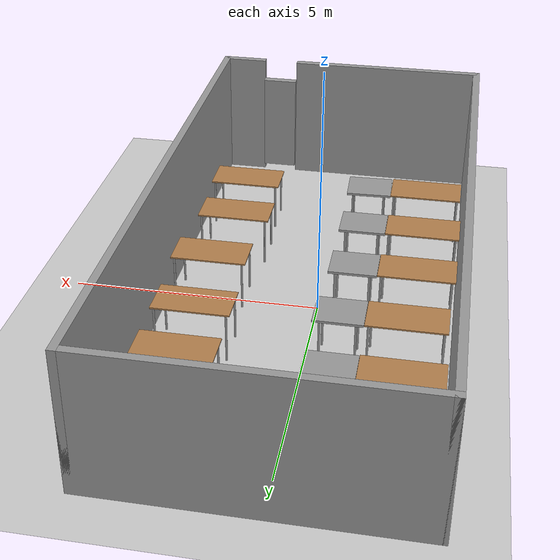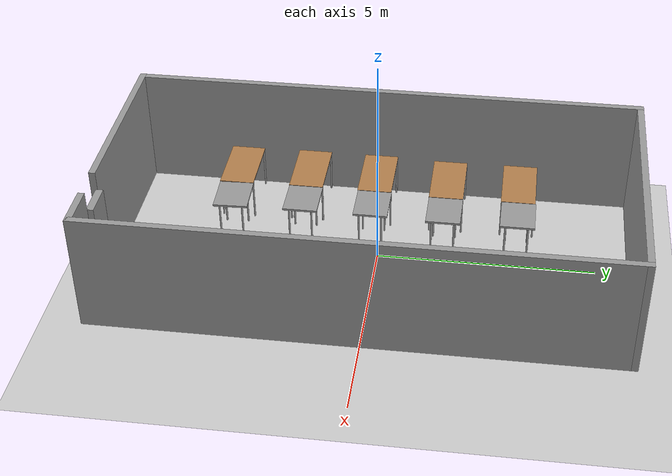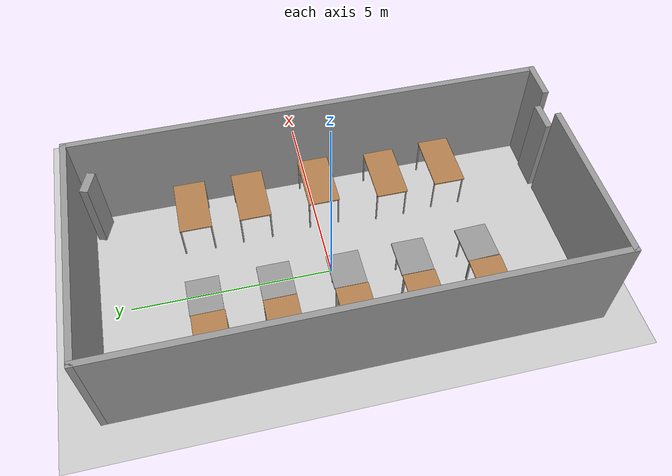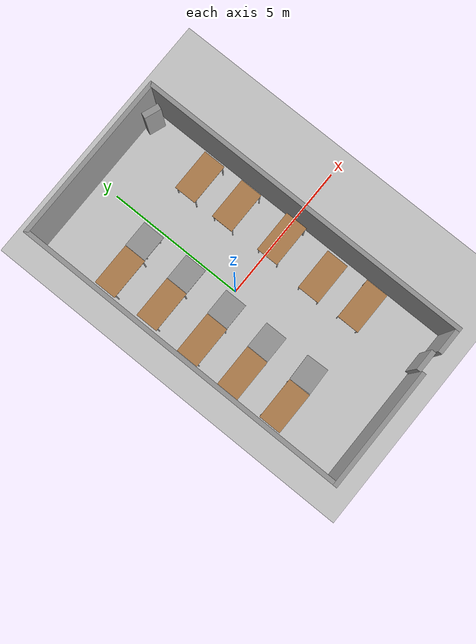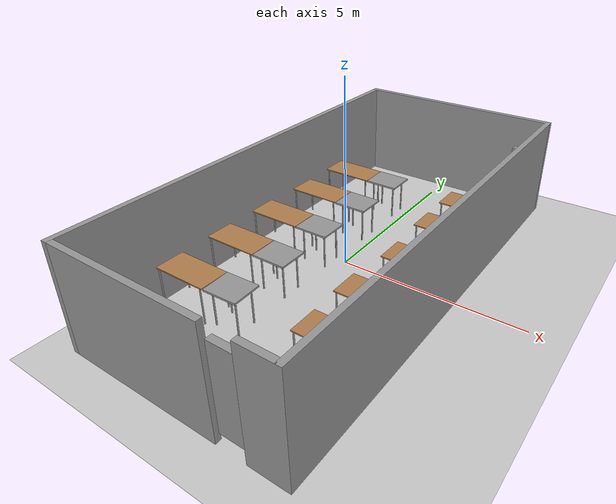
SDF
<sdf version="1.7">
 <world name="default">
  <light name="sun" type="directional">
   <pose>0 0 10 0 -0 0</pose>
   <diffuse>0.8 0.8 0.8 1</diffuse>
   <specular>0.2 0.2 0.2 1</specular>
   <attenuation>
    <range>1000</range>
    <constant>0.9</constant>
    <linear>0.01</linear>
    <quadratic>0.001</quadratic>
   </attenuation>
   <direction>-0.5 0.1 -0.9</direction>
   <spot><inner_angle>0</inner_angle><outer_angle>0</outer_angle><falloff>0</falloff></spot>
  </light>
  <model name="ground_plane">
   <static>1</static>
   <link name="link">
    <collision name="collision">
     <geometry><plane><normal>0 0 1</normal><size>100 100</size></plane></geometry>
     <surface>
      <contact><collide_bitmask>65535</collide_bitmask></contact>
      <friction><ode><mu>100</mu><mu2>50</mu2></ode></friction>
     </surface>
    </collision>
    <visual name="visual">
     <cast_shadows>0</cast_shadows>
     <geometry><plane><normal>0 0 1</normal><size>100 100</size></plane></geometry>
     <material>
      <script><uri>file://media/materials/scripts/gazebo.material</uri><name>Gazebo/Grey</name></script>
     </material>
    </visual>
   </link>
  </model>
  <gravity>0 0 -9.8</gravity>
  <magnetic_field>6e-06 2.3e-05 -4.2e-05</magnetic_field>
  <atmosphere type="adiabatic"/>
  <physics type="ode">
   <max_step_size>0.001</max_step_size>
   <real_time_factor>1</real_time_factor>
   <real_time_update_rate>1000</real_time_update_rate>
  </physics>
  <scene><ambient>0.4 0.4 0.4 1</ambient><background>0.7 0.7 0.7 1</background><shadows>1</shadows></scene>
  <spherical_coordinates>
   <surface_model>EARTH_WGS84</surface_model>
   <latitude_deg>0</latitude_deg>
   <longitude_deg>0</longitude_deg>
   <elevation>0</elevation>
   <heading_deg>0</heading_deg>
  </spherical_coordinates>
  <model name="yh_room">
   <pose>0.178557 -0.120758 0 0 -0 0</pose>
   <link name="Wall_13">
    <collision name="Wall_13_Collision">
     <geometry><box><size>6 0.15 2.8</size></box></geometry>
     <pose>0 0 1.4 0 -0 0</pose>
    </collision>
    <visual name="Wall_13_Visual">
     <pose>0 0 1.4 0 -0 0</pose>
     <geometry><box><size>6 0.15 2.8</size></box></geometry>
     <material>
      <script><uri>file://media/materials/scripts/gazebo.material</uri><name>Gazebo/Grey</name></script>
      <ambient>1 1 1 1</ambient>
     </material>
     <meta><layer>0</layer></meta>
    </visual>
    <pose>-0 5.925 0 0 -0 0</pose>
   </link>
   <link name="Wall_15">
    <collision name="Wall_15_Collision">
     <geometry><box><size>12 0.15 2.8</size></box></geometry>
     <pose>0 0 1.4 0 -0 0</pose>
    </collision>
    <visual name="Wall_15_Visual">
     <pose>0 0 1.4 0 -0 0</pose>
     <geometry><box><size>12 0.15 2.8</size></box></geometry>
     <material>
      <script><uri>file://media/materials/scripts/gazebo.material</uri><name>Gazebo/Grey</name></script>
      <ambient>1 1 1 1</ambient>
     </material>
     <meta><layer>0</layer></meta>
    </visual>
    <pose>-2.925 0 0 0 -0 -1.5708</pose>
   </link>
   <link name="Wall_18">
    <collision name="Wall_18_Collision">
     <geometry><box><size>12 0.15 2.8</size></box></geometry>
     <pose>0 0 1.4 0 -0 0</pose>
    </collision>
    <visual name="Wall_18_Visual">
     <pose>0 0 1.4 0 -0 0</pose>
     <geometry><box><size>12 0.15 2.8</size></box></geometry>
     <material>
      <script><uri>file://media/materials/scripts/gazebo.material</uri><name>Gazebo/Grey</name></script>
      <ambient>1 1 1 1</ambient>
     </material>
     <meta><layer>0</layer></meta>
    </visual>
    <pose>2.925 0 0 0 -0 1.5708</pose>
   </link>
   <link name="Wall_21">
    <collision name="Wall_21_Collision">
     <geometry><box><size>1 0.15 2.8</size></box></geometry>
     <pose>0 0 1.4 0 -0 0</pose>
    </collision>
    <visual name="Wall_21_Visual">
     <pose>0 0 1.4 0 -0 0</pose>
     <geometry><box><size>1 0.15 2.8</size></box></geometry>
     <material>
      <script><uri>file://media/materials/scripts/gazebo.material</uri><name>Gazebo/Grey</name></script>
      <ambient>1 1 1 1</ambient>
     </material>
     <meta><layer>0</layer></meta>
    </visual>
    <pose>2.5 -5.925 0 0 -0 3.14159</pose>
   </link>
   <link name="Wall_23">
    <collision name="Wall_23_Collision">
     <geometry><box><size>4.25 0.15 2.8</size></box></geometry>
     <pose>0 0 1.4 0 -0 0</pose>
    </collision>
    <visual name="Wall_23_Visual">
     <pose>0 0 1.4 0 -0 0</pose>
     <geometry><box><size>4.25 0.15 2.8</size></box></geometry>
     <material>
      <script><uri>file://media/materials/scripts/gazebo.material</uri><name>Gazebo/Grey</name></script>
      <ambient>1 1 1 1</ambient>
     </material>
     <meta><layer>0</layer></meta>
    </visual>
    <pose>-0.875 -5.925 0 0 -0 0</pose>
   </link>
   <static>1</static>
  </model>
  <model name="table">
   <static>1</static>
   <link name="link">
    <collision name="surface">
     <pose>0 0 1 0 -0 0</pose>
     <geometry><box><size>1.5 0.8 0.03</size></box></geometry>
     <surface><friction><ode><mu>0.6</mu><mu2>0.6</mu2></ode></friction></surface>
    </collision>
    <visual name="visual1">
     <pose>0 0 1 0 -0 0</pose>
     <geometry><box><size>1.5 0.8 0.03</size></box></geometry>
     <material>
      <script><uri>file://media/materials/scripts/gazebo.material</uri><name>Gazebo/Wood</name></script>
     </material>
    </visual>
    <collision name="front_left_leg">
     <pose>0.68 0.38 0.5 0 -0 0</pose>
     <geometry><cylinder><radius>0.02</radius><length>1</length></cylinder></geometry>
    </collision>
    <visual name="front_left_leg">
     <pose>0.68 0.38 0.5 0 -0 0</pose>
     <geometry><cylinder><radius>0.02</radius><length>1</length></cylinder></geometry>
     <material>
      <script><uri>file://media/materials/scripts/gazebo.material</uri><name>Gazebo/Grey</name></script>
     </material>
    </visual>
    <collision name="front_right_leg">
     <pose>0.68 -0.38 0.5 0 -0 0</pose>
     <geometry><cylinder><radius>0.02</radius><length>1</length></cylinder></geometry>
    </collision>
    <visual name="front_right_leg">
     <pose>0.68 -0.38 0.5 0 -0 0</pose>
     <geometry><cylinder><radius>0.02</radius><length>1</length></cylinder></geometry>
     <material>
      <script><uri>file://media/materials/scripts/gazebo.material</uri><name>Gazebo/Grey</name></script>
     </material>
    </visual>
    <collision name="back_right_leg">
     <pose>-0.68 -0.38 0.5 0 -0 0</pose>
     <geometry><cylinder><radius>0.02</radius><length>1</length></cylinder></geometry>
    </collision>
    <visual name="back_right_leg">
     <pose>-0.68 -0.38 0.5 0 -0 0</pose>
     <geometry><cylinder><radius>0.02</radius><length>1</length></cylinder></geometry>
     <material>
      <script><uri>file://media/materials/scripts/gazebo.material</uri><name>Gazebo/Grey</name></script>
     </material>
    </visual>
    <collision name="back_left_leg">
     <pose>-0.68 0.38 0.5 0 -0 0</pose>
     <geometry><cylinder><radius>0.02</radius><length>1</length></cylinder></geometry>
    </collision>
    <visual name="back_left_leg">
     <pose>-0.68 0.38 0.5 0 -0 0</pose>
     <geometry><cylinder><radius>0.02</radius><length>1</length></cylinder></geometry>
     <material>
      <script><uri>file://media/materials/scripts/gazebo.material</uri><name>Gazebo/Grey</name></script>
     </material>
    </visual>
   </link>
   <pose>-1.86656 3.15657 0 0 -0 0</pose>
  </model>
  <model name="table_clone">
   <static>1</static>
   <link name="link">
    <collision name="surface">
     <pose>0 0 1 0 -0 0</pose>
     <geometry><box><size>1.5 0.8 0.03</size></box></geometry>
     <surface><friction><ode><mu>0.6</mu><mu2>0.6</mu2></ode></friction></surface>
    </collision>
    <visual name="visual1">
     <pose>0 0 1 0 -0 0</pose>
     <geometry><box><size>1.5 0.8 0.03</size></box></geometry>
     <material>
      <script><uri>file://media/materials/scripts/gazebo.material</uri><name>Gazebo/Wood</name></script>
     </material>
    </visual>
    <collision name="front_left_leg">
     <pose>0.68 0.38 0.5 0 -0 0</pose>
     <geometry><cylinder><radius>0.02</radius><length>1</length></cylinder></geometry>
    </collision>
    <visual name="front_left_leg">
     <pose>0.68 0.38 0.5 0 -0 0</pose>
     <geometry><cylinder><radius>0.02</radius><length>1</length></cylinder></geometry>
     <material>
      <script><uri>file://media/materials/scripts/gazebo.material</uri><name>Gazebo/Grey</name></script>
     </material>
    </visual>
    <collision name="front_right_leg">
     <pose>0.68 -0.38 0.5 0 -0 0</pose>
     <geometry><cylinder><radius>0.02</radius><length>1</length></cylinder></geometry>
    </collision>
    <visual name="front_right_leg">
     <pose>0.68 -0.38 0.5 0 -0 0</pose>
     <geometry><cylinder><radius>0.02</radius><length>1</length></cylinder></geometry>
     <material>
      <script><uri>file://media/materials/scripts/gazebo.material</uri><name>Gazebo/Grey</name></script>
     </material>
    </visual>
    <collision name="back_right_leg">
     <pose>-0.68 -0.38 0.5 0 -0 0</pose>
     <geometry><cylinder><radius>0.02</radius><length>1</length></cylinder></geometry>
    </collision>
    <visual name="back_right_leg">
     <pose>-0.68 -0.38 0.5 0 -0 0</pose>
     <geometry><cylinder><radius>0.02</radius><length>1</length></cylinder></geometry>
     <material>
      <script><uri>file://media/materials/scripts/gazebo.material</uri><name>Gazebo/Grey</name></script>
     </material>
    </visual>
    <collision name="back_left_leg">
     <pose>-0.68 0.38 0.5 0 -0 0</pose>
     <geometry><cylinder><radius>0.02</radius><length>1</length></cylinder></geometry>
    </collision>
    <visual name="back_left_leg">
     <pose>-0.68 0.38 0.5 0 -0 0</pose>
     <geometry><cylinder><radius>0.02</radius><length>1</length></cylinder></geometry>
     <material>
      <script><uri>file://media/materials/scripts/gazebo.material</uri><name>Gazebo/Grey</name></script>
     </material>
    </visual>
   </link>
   <pose>2.06637 3.12648 0 0 -0 0</pose>
  </model>
  <model name="table_clone_0">
   <static>1</static>
   <link name="link">
    <collision name="surface">
     <pose>0 0 1 0 -0 0</pose>
     <geometry><box><size>1.5 0.8 0.03</size></box></geometry>
     <surface><friction><ode><mu>0.6</mu><mu2>0.6</mu2></ode></friction></surface>
    </collision>
    <visual name="visual1">
     <pose>0 0 1 0 -0 0</pose>
     <geometry><box><size>1.5 0.8 0.03</size></box></geometry>
     <material>
      <script><uri>file://media/materials/scripts/gazebo.material</uri><name>Gazebo/Wood</name></script>
     </material>
    </visual>
    <collision name="front_left_leg">
     <pose>0.68 0.38 0.5 0 -0 0</pose>
     <geometry><cylinder><radius>0.02</radius><length>1</length></cylinder></geometry>
    </collision>
    <visual name="front_left_leg">
     <pose>0.68 0.38 0.5 0 -0 0</pose>
     <geometry><cylinder><radius>0.02</radius><length>1</length></cylinder></geometry>
     <material>
      <script><uri>file://media/materials/scripts/gazebo.material</uri><name>Gazebo/Grey</name></script>
     </material>
    </visual>
    <collision name="front_right_leg">
     <pose>0.68 -0.38 0.5 0 -0 0</pose>
     <geometry><cylinder><radius>0.02</radius><length>1</length></cylinder></geometry>
    </collision>
    <visual name="front_right_leg">
     <pose>0.68 -0.38 0.5 0 -0 0</pose>
     <geometry><cylinder><radius>0.02</radius><length>1</length></cylinder></geometry>
     <material>
      <script><uri>file://media/materials/scripts/gazebo.material</uri><name>Gazebo/Grey</name></script>
     </material>
    </visual>
    <collision name="back_right_leg">
     <pose>-0.68 -0.38 0.5 0 -0 0</pose>
     <geometry><cylinder><radius>0.02</radius><length>1</length></cylinder></geometry>
    </collision>
    <visual name="back_right_leg">
     <pose>-0.68 -0.38 0.5 0 -0 0</pose>
     <geometry><cylinder><radius>0.02</radius><length>1</length></cylinder></geometry>
     <material>
      <script><uri>file://media/materials/scripts/gazebo.material</uri><name>Gazebo/Grey</name></script>
     </material>
    </visual>
    <collision name="back_left_leg">
     <pose>-0.68 0.38 0.5 0 -0 0</pose>
     <geometry><cylinder><radius>0.02</radius><length>1</length></cylinder></geometry>
    </collision>
    <visual name="back_left_leg">
     <pose>-0.68 0.38 0.5 0 -0 0</pose>
     <geometry><cylinder><radius>0.02</radius><length>1</length></cylinder></geometry>
     <material>
      <script><uri>file://media/materials/scripts/gazebo.material</uri><name>Gazebo/Grey</name></script>
     </material>
    </visual>
   </link>
   <pose>-1.84278 1.47445 0 0 -0 0</pose>
  </model>
  <model name="table_clone_1">
   <static>1</static>
   <link name="link">
    <collision name="surface">
     <pose>0 0 1 0 -0 0</pose>
     <geometry><box><size>1.5 0.8 0.03</size></box></geometry>
     <surface><friction><ode><mu>0.6</mu><mu2>0.6</mu2></ode></friction></surface>
    </collision>
    <visual name="visual1">
     <pose>0 0 1 0 -0 0</pose>
     <geometry><box><size>1.5 0.8 0.03</size></box></geometry>
     <material>
      <script><uri>file://media/materials/scripts/gazebo.material</uri><name>Gazebo/Wood</name></script>
     </material>
    </visual>
    <collision name="front_left_leg">
     <pose>0.68 0.38 0.5 0 -0 0</pose>
     <geometry><cylinder><radius>0.02</radius><length>1</length></cylinder></geometry>
    </collision>
    <visual name="front_left_leg">
     <pose>0.68 0.38 0.5 0 -0 0</pose>
     <geometry><cylinder><radius>0.02</radius><length>1</length></cylinder></geometry>
     <material>
      <script><uri>file://media/materials/scripts/gazebo.material</uri><name>Gazebo/Grey</name></script>
     </material>
    </visual>
    <collision name="front_right_leg">
     <pose>0.68 -0.38 0.5 0 -0 0</pose>
     <geometry><cylinder><radius>0.02</radius><length>1</length></cylinder></geometry>
    </collision>
    <visual name="front_right_leg">
     <pose>0.68 -0.38 0.5 0 -0 0</pose>
     <geometry><cylinder><radius>0.02</radius><length>1</length></cylinder></geometry>
     <material>
      <script><uri>file://media/materials/scripts/gazebo.material</uri><name>Gazebo/Grey</name></script>
     </material>
    </visual>
    <collision name="back_right_leg">
     <pose>-0.68 -0.38 0.5 0 -0 0</pose>
     <geometry><cylinder><radius>0.02</radius><length>1</length></cylinder></geometry>
    </collision>
    <visual name="back_right_leg">
     <pose>-0.68 -0.38 0.5 0 -0 0</pose>
     <geometry><cylinder><radius>0.02</radius><length>1</length></cylinder></geometry>
     <material>
      <script><uri>file://media/materials/scripts/gazebo.material</uri><name>Gazebo/Grey</name></script>
     </material>
    </visual>
    <collision name="back_left_leg">
     <pose>-0.68 0.38 0.5 0 -0 0</pose>
     <geometry><cylinder><radius>0.02</radius><length>1</length></cylinder></geometry>
    </collision>
    <visual name="back_left_leg">
     <pose>-0.68 0.38 0.5 0 -0 0</pose>
     <geometry><cylinder><radius>0.02</radius><length>1</length></cylinder></geometry>
     <material>
      <script><uri>file://media/materials/scripts/gazebo.material</uri><name>Gazebo/Grey</name></script>
     </material>
    </visual>
   </link>
   <pose>2.08707 1.6284 0 0 -0 0</pose>
  </model>
  <model name="table_clone_2">
   <static>1</static>
   <link name="link">
    <collision name="surface">
     <pose>0 0 1 0 -0 0</pose>
     <geometry><box><size>1.5 0.8 0.03</size></box></geometry>
     <surface><friction><ode><mu>0.6</mu><mu2>0.6</mu2></ode></friction></surface>
    </collision>
    <visual name="visual1">
     <pose>0 0 1 0 -0 0</pose>
     <geometry><box><size>1.5 0.8 0.03</size></box></geometry>
     <material>
      <script><uri>file://media/materials/scripts/gazebo.material</uri><name>Gazebo/Wood</name></script>
     </material>
    </visual>
    <collision name="front_left_leg">
     <pose>0.68 0.38 0.5 0 -0 0</pose>
     <geometry><cylinder><radius>0.02</radius><length>1</length></cylinder></geometry>
    </collision>
    <visual name="front_left_leg">
     <pose>0.68 0.38 0.5 0 -0 0</pose>
     <geometry><cylinder><radius>0.02</radius><length>1</length></cylinder></geometry>
     <material>
      <script><uri>file://media/materials/scripts/gazebo.material</uri><name>Gazebo/Grey</name></script>
     </material>
    </visual>
    <collision name="front_right_leg">
     <pose>0.68 -0.38 0.5 0 -0 0</pose>
     <geometry><cylinder><radius>0.02</radius><length>1</length></cylinder></geometry>
    </collision>
    <visual name="front_right_leg">
     <pose>0.68 -0.38 0.5 0 -0 0</pose>
     <geometry><cylinder><radius>0.02</radius><length>1</length></cylinder></geometry>
     <material>
      <script><uri>file://media/materials/scripts/gazebo.material</uri><name>Gazebo/Grey</name></script>
     </material>
    </visual>
    <collision name="back_right_leg">
     <pose>-0.68 -0.38 0.5 0 -0 0</pose>
     <geometry><cylinder><radius>0.02</radius><length>1</length></cylinder></geometry>
    </collision>
    <visual name="back_right_leg">
     <pose>-0.68 -0.38 0.5 0 -0 0</pose>
     <geometry><cylinder><radius>0.02</radius><length>1</length></cylinder></geometry>
     <material>
      <script><uri>file://media/materials/scripts/gazebo.material</uri><name>Gazebo/Grey</name></script>
     </material>
    </visual>
    <collision name="back_left_leg">
     <pose>-0.68 0.38 0.5 0 -0 0</pose>
     <geometry><cylinder><radius>0.02</radius><length>1</length></cylinder></geometry>
    </collision>
    <visual name="back_left_leg">
     <pose>-0.68 0.38 0.5 0 -0 0</pose>
     <geometry><cylinder><radius>0.02</radius><length>1</length></cylinder></geometry>
     <material>
      <script><uri>file://media/materials/scripts/gazebo.material</uri><name>Gazebo/Grey</name></script>
     </material>
    </visual>
   </link>
   <pose>-1.90852 -0.220594 0 0 -0 0</pose>
  </model>
  <model name="table_clone_3">
   <static>1</static>
   <link name="link">
    <collision name="surface">
     <pose>0 0 1 0 -0 0</pose>
     <geometry><box><size>1.5 0.8 0.03</size></box></geometry>
     <surface><friction><ode><mu>0.6</mu><mu2>0.6</mu2></ode></friction></surface>
    </collision>
    <visual name="visual1">
     <pose>0 0 1 0 -0 0</pose>
     <geometry><box><size>1.5 0.8 0.03</size></box></geometry>
     <material>
      <script><uri>file://media/materials/scripts/gazebo.material</uri><name>Gazebo/Wood</name></script>
     </material>
    </visual>
    <collision name="front_left_leg">
     <pose>0.68 0.38 0.5 0 -0 0</pose>
     <geometry><cylinder><radius>0.02</radius><length>1</length></cylinder></geometry>
    </collision>
    <visual name="front_left_leg">
     <pose>0.68 0.38 0.5 0 -0 0</pose>
     <geometry><cylinder><radius>0.02</radius><length>1</length></cylinder></geometry>
     <material>
      <script><uri>file://media/materials/scripts/gazebo.material</uri><name>Gazebo/Grey</name></script>
     </material>
    </visual>
    <collision name="front_right_leg">
     <pose>0.68 -0.38 0.5 0 -0 0</pose>
     <geometry><cylinder><radius>0.02</radius><length>1</length></cylinder></geometry>
    </collision>
    <visual name="front_right_leg">
     <pose>0.68 -0.38 0.5 0 -0 0</pose>
     <geometry><cylinder><radius>0.02</radius><length>1</length></cylinder></geometry>
     <material>
      <script><uri>file://media/materials/scripts/gazebo.material</uri><name>Gazebo/Grey</name></script>
     </material>
    </visual>
    <collision name="back_right_leg">
     <pose>-0.68 -0.38 0.5 0 -0 0</pose>
     <geometry><cylinder><radius>0.02</radius><length>1</length></cylinder></geometry>
    </collision>
    <visual name="back_right_leg">
     <pose>-0.68 -0.38 0.5 0 -0 0</pose>
     <geometry><cylinder><radius>0.02</radius><length>1</length></cylinder></geometry>
     <material>
      <script><uri>file://media/materials/scripts/gazebo.material</uri><name>Gazebo/Grey</name></script>
     </material>
    </visual>
    <collision name="back_left_leg">
     <pose>-0.68 0.38 0.5 0 -0 0</pose>
     <geometry><cylinder><radius>0.02</radius><length>1</length></cylinder></geometry>
    </collision>
    <visual name="back_left_leg">
     <pose>-0.68 0.38 0.5 0 -0 0</pose>
     <geometry><cylinder><radius>0.02</radius><length>1</length></cylinder></geometry>
     <material>
      <script><uri>file://media/materials/scripts/gazebo.material</uri><name>Gazebo/Grey</name></script>
     </material>
    </visual>
   </link>
   <pose>-1.91403 -1.85132 0 0 -0 0</pose>
  </model>
  <model name="table_clone_4">
   <static>1</static>
   <link name="link">
    <collision name="surface">
     <pose>0 0 1 0 -0 0</pose>
     <geometry><box><size>1.5 0.8 0.03</size></box></geometry>
     <surface><friction><ode><mu>0.6</mu><mu2>0.6</mu2></ode></friction></surface>
    </collision>
    <visual name="visual1">
     <pose>0 0 1 0 -0 0</pose>
     <geometry><box><size>1.5 0.8 0.03</size></box></geometry>
     <material>
      <script><uri>file://media/materials/scripts/gazebo.material</uri><name>Gazebo/Wood</name></script>
     </material>
    </visual>
    <collision name="front_left_leg">
     <pose>0.68 0.38 0.5 0 -0 0</pose>
     <geometry><cylinder><radius>0.02</radius><length>1</length></cylinder></geometry>
    </collision>
    <visual name="front_left_leg">
     <pose>0.68 0.38 0.5 0 -0 0</pose>
     <geometry><cylinder><radius>0.02</radius><length>1</length></cylinder></geometry>
     <material>
      <script><uri>file://media/materials/scripts/gazebo.material</uri><name>Gazebo/Grey</name></script>
     </material>
    </visual>
    <collision name="front_right_leg">
     <pose>0.68 -0.38 0.5 0 -0 0</pose>
     <geometry><cylinder><radius>0.02</radius><length>1</length></cylinder></geometry>
    </collision>
    <visual name="front_right_leg">
     <pose>0.68 -0.38 0.5 0 -0 0</pose>
     <geometry><cylinder><radius>0.02</radius><length>1</length></cylinder></geometry>
     <material>
      <script><uri>file://media/materials/scripts/gazebo.material</uri><name>Gazebo/Grey</name></script>
     </material>
    </visual>
    <collision name="back_right_leg">
     <pose>-0.68 -0.38 0.5 0 -0 0</pose>
     <geometry><cylinder><radius>0.02</radius><length>1</length></cylinder></geometry>
    </collision>
    <visual name="back_right_leg">
     <pose>-0.68 -0.38 0.5 0 -0 0</pose>
     <geometry><cylinder><radius>0.02</radius><length>1</length></cylinder></geometry>
     <material>
      <script><uri>file://media/materials/scripts/gazebo.material</uri><name>Gazebo/Grey</name></script>
     </material>
    </visual>
    <collision name="back_left_leg">
     <pose>-0.68 0.38 0.5 0 -0 0</pose>
     <geometry><cylinder><radius>0.02</radius><length>1</length></cylinder></geometry>
    </collision>
    <visual name="back_left_leg">
     <pose>-0.68 0.38 0.5 0 -0 0</pose>
     <geometry><cylinder><radius>0.02</radius><length>1</length></cylinder></geometry>
     <material>
      <script><uri>file://media/materials/scripts/gazebo.material</uri><name>Gazebo/Grey</name></script>
     </material>
    </visual>
   </link>
   <pose>-1.87955 -3.51213 0 0 -0 0</pose>
  </model>
  <model name="table_clone_5">
   <static>1</static>
   <link name="link">
    <collision name="surface">
     <pose>0 0 1 0 -0 0</pose>
     <geometry><box><size>1.5 0.8 0.03</size></box></geometry>
     <surface><friction><ode><mu>0.6</mu><mu2>0.6</mu2></ode></friction></surface>
    </collision>
    <visual name="visual1">
     <pose>0 0 1 0 -0 0</pose>
     <geometry><box><size>1.5 0.8 0.03</size></box></geometry>
     <material>
      <script><uri>file://media/materials/scripts/gazebo.material</uri><name>Gazebo/Wood</name></script>
     </material>
    </visual>
    <collision name="front_left_leg">
     <pose>0.68 0.38 0.5 0 -0 0</pose>
     <geometry><cylinder><radius>0.02</radius><length>1</length></cylinder></geometry>
    </collision>
    <visual name="front_left_leg">
     <pose>0.68 0.38 0.5 0 -0 0</pose>
     <geometry><cylinder><radius>0.02</radius><length>1</length></cylinder></geometry>
     <material>
      <script><uri>file://media/materials/scripts/gazebo.material</uri><name>Gazebo/Grey</name></script>
     </material>
    </visual>
    <collision name="front_right_leg">
     <pose>0.68 -0.38 0.5 0 -0 0</pose>
     <geometry><cylinder><radius>0.02</radius><length>1</length></cylinder></geometry>
    </collision>
    <visual name="front_right_leg">
     <pose>0.68 -0.38 0.5 0 -0 0</pose>
     <geometry><cylinder><radius>0.02</radius><length>1</length></cylinder></geometry>
     <material>
      <script><uri>file://media/materials/scripts/gazebo.material</uri><name>Gazebo/Grey</name></script>
     </material>
    </visual>
    <collision name="back_right_leg">
     <pose>-0.68 -0.38 0.5 0 -0 0</pose>
     <geometry><cylinder><radius>0.02</radius><length>1</length></cylinder></geometry>
    </collision>
    <visual name="back_right_leg">
     <pose>-0.68 -0.38 0.5 0 -0 0</pose>
     <geometry><cylinder><radius>0.02</radius><length>1</length></cylinder></geometry>
     <material>
      <script><uri>file://media/materials/scripts/gazebo.material</uri><name>Gazebo/Grey</name></script>
     </material>
    </visual>
    <collision name="back_left_leg">
     <pose>-0.68 0.38 0.5 0 -0 0</pose>
     <geometry><cylinder><radius>0.02</radius><length>1</length></cylinder></geometry>
    </collision>
    <visual name="back_left_leg">
     <pose>-0.68 0.38 0.5 0 -0 0</pose>
     <geometry><cylinder><radius>0.02</radius><length>1</length></cylinder></geometry>
     <material>
      <script><uri>file://media/materials/scripts/gazebo.material</uri><name>Gazebo/Grey</name></script>
     </material>
    </visual>
   </link>
   <pose>2.16456 -0.152006 0 0 -0 0</pose>
  </model>
  <model name="table_clone_6">
   <static>1</static>
   <link name="link">
    <collision name="surface">
     <pose>0 0 1 0 -0 0</pose>
     <geometry><box><size>1.5 0.8 0.03</size></box></geometry>
     <surface><friction><ode><mu>0.6</mu><mu2>0.6</mu2></ode></friction></surface>
    </collision>
    <visual name="visual1">
     <pose>0 0 1 0 -0 0</pose>
     <geometry><box><size>1.5 0.8 0.03</size></box></geometry>
     <material>
      <script><uri>file://media/materials/scripts/gazebo.material</uri><name>Gazebo/Wood</name></script>
     </material>
    </visual>
    <collision name="front_left_leg">
     <pose>0.68 0.38 0.5 0 -0 0</pose>
     <geometry><cylinder><radius>0.02</radius><length>1</length></cylinder></geometry>
    </collision>
    <visual name="front_left_leg">
     <pose>0.68 0.38 0.5 0 -0 0</pose>
     <geometry><cylinder><radius>0.02</radius><length>1</length></cylinder></geometry>
     <material>
      <script><uri>file://media/materials/scripts/gazebo.material</uri><name>Gazebo/Grey</name></script>
     </material>
    </visual>
    <collision name="front_right_leg">
     <pose>0.68 -0.38 0.5 0 -0 0</pose>
     <geometry><cylinder><radius>0.02</radius><length>1</length></cylinder></geometry>
    </collision>
    <visual name="front_right_leg">
     <pose>0.68 -0.38 0.5 0 -0 0</pose>
     <geometry><cylinder><radius>0.02</radius><length>1</length></cylinder></geometry>
     <material>
      <script><uri>file://media/materials/scripts/gazebo.material</uri><name>Gazebo/Grey</name></script>
     </material>
    </visual>
    <collision name="back_right_leg">
     <pose>-0.68 -0.38 0.5 0 -0 0</pose>
     <geometry><cylinder><radius>0.02</radius><length>1</length></cylinder></geometry>
    </collision>
    <visual name="back_right_leg">
     <pose>-0.68 -0.38 0.5 0 -0 0</pose>
     <geometry><cylinder><radius>0.02</radius><length>1</length></cylinder></geometry>
     <material>
      <script><uri>file://media/materials/scripts/gazebo.material</uri><name>Gazebo/Grey</name></script>
     </material>
    </visual>
    <collision name="back_left_leg">
     <pose>-0.68 0.38 0.5 0 -0 0</pose>
     <geometry><cylinder><radius>0.02</radius><length>1</length></cylinder></geometry>
    </collision>
    <visual name="back_left_leg">
     <pose>-0.68 0.38 0.5 0 -0 0</pose>
     <geometry><cylinder><radius>0.02</radius><length>1</length></cylinder></geometry>
     <material>
      <script><uri>file://media/materials/scripts/gazebo.material</uri><name>Gazebo/Grey</name></script>
     </material>
    </visual>
   </link>
   <pose>2.03753 -1.9148 0 0 -0 0</pose>
  </model>
  <model name="table_clone_7">
   <static>1</static>
   <link name="link">
    <collision name="surface">
     <pose>0 0 1 0 -0 0</pose>
     <geometry><box><size>1.5 0.8 0.03</size></box></geometry>
     <surface><friction><ode><mu>0.6</mu><mu2>0.6</mu2></ode></friction></surface>
    </collision>
    <visual name="visual1">
     <pose>0 0 1 0 -0 0</pose>
     <geometry><box><size>1.5 0.8 0.03</size></box></geometry>
     <material>
      <script><uri>file://media/materials/scripts/gazebo.material</uri><name>Gazebo/Wood</name></script>
     </material>
    </visual>
    <collision name="front_left_leg">
     <pose>0.68 0.38 0.5 0 -0 0</pose>
     <geometry><cylinder><radius>0.02</radius><length>1</length></cylinder></geometry>
    </collision>
    <visual name="front_left_leg">
     <pose>0.68 0.38 0.5 0 -0 0</pose>
     <geometry><cylinder><radius>0.02</radius><length>1</length></cylinder></geometry>
     <material>
      <script><uri>file://media/materials/scripts/gazebo.material</uri><name>Gazebo/Grey</name></script>
     </material>
    </visual>
    <collision name="front_right_leg">
     <pose>0.68 -0.38 0.5 0 -0 0</pose>
     <geometry><cylinder><radius>0.02</radius><length>1</length></cylinder></geometry>
    </collision>
    <visual name="front_right_leg">
     <pose>0.68 -0.38 0.5 0 -0 0</pose>
     <geometry><cylinder><radius>0.02</radius><length>1</length></cylinder></geometry>
     <material>
      <script><uri>file://media/materials/scripts/gazebo.material</uri><name>Gazebo/Grey</name></script>
     </material>
    </visual>
    <collision name="back_right_leg">
     <pose>-0.68 -0.38 0.5 0 -0 0</pose>
     <geometry><cylinder><radius>0.02</radius><length>1</length></cylinder></geometry>
    </collision>
    <visual name="back_right_leg">
     <pose>-0.68 -0.38 0.5 0 -0 0</pose>
     <geometry><cylinder><radius>0.02</radius><length>1</length></cylinder></geometry>
     <material>
      <script><uri>file://media/materials/scripts/gazebo.material</uri><name>Gazebo/Grey</name></script>
     </material>
    </visual>
    <collision name="back_left_leg">
     <pose>-0.68 0.38 0.5 0 -0 0</pose>
     <geometry><cylinder><radius>0.02</radius><length>1</length></cylinder></geometry>
    </collision>
    <visual name="back_left_leg">
     <pose>-0.68 0.38 0.5 0 -0 0</pose>
     <geometry><cylinder><radius>0.02</radius><length>1</length></cylinder></geometry>
     <material>
      <script><uri>file://media/materials/scripts/gazebo.material</uri><name>Gazebo/Grey</name></script>
     </material>
    </visual>
   </link>
   <pose>2.09447 -3.46015 0 0 -0 0</pose>
  </model>
  <model name="503smalldesk">
   <link name="link">
    <inertial>
     <mass>0.0369798</mass>
     <inertia>
      <ixx>0.00196522</ixx>
      <ixy>0</ixy>
      <ixz>0</ixz>
      <iyy>0.00276457</iyy>
      <iyz>0</iyz>
      <izz>0.00471494</izz>
     </inertia>
    </inertial>
    <pose>-0.646649 -1.26581 0.489389 0 -0 0</pose>
    <visual name="visual">
     <geometry><box><size>0.945885 0.797062 0.049088</size></box></geometry>
     <material>
      <script><name>Gazebo/Grey</name><uri>file://media/materials/scripts/gazebo.material</uri></script>
      <shader type="pixel"/>
      <emissive>0 0 0 1</emissive>
     </material>
    </visual>
    <collision name="collision">
     <geometry><box><size>0.945885 0.797062 0.049088</size></box></geometry>
     <surface>
      <friction>
       <ode><mu>1</mu><mu2>1</mu2><fdir1>0 0 0</fdir1><slip1>0</slip1><slip2>0</slip2></ode>
       <torsional>
        <coefficient>1</coefficient>
        <patch_radius>0</patch_radius>
        <surface_radius>0</surface_radius>
        <use_patch_radius>1</use_patch_radius>
        <ode><slip>0</slip></ode>
       </torsional>
      </friction>
      <bounce><restitution_coefficient>0</restitution_coefficient><threshold>1e+06</threshold></bounce>
      <contact>
       <collide_without_contact>0</collide_without_contact>
       <collide_without_contact_bitmask>1</collide_without_contact_bitmask>
       <collide_bitmask>1</collide_bitmask>
       <ode>
        <soft_cfm>0</soft_cfm>
        <soft_erp>0.2</soft_erp>
        <kp>1e+13</kp>
        <kd>1</kd>
        <max_vel>0.01</max_vel>
        <min_depth>0</min_depth>
       </ode>
       <bullet>
        <split_impulse>1</split_impulse>
        <split_impulse_penetration_threshold>-0.01</split_impulse_penetration_threshold>
        <soft_cfm>0</soft_cfm>
        <soft_erp>0.2</soft_erp>
        <kp>1e+13</kp>
        <kd>1</kd>
       </bullet>
      </contact>
     </surface>
    </collision>
   </link>
   <link name="link_0">
    <inertial>
     <mass>0.00191364</mass>
     <inertia>
      <ixx>0.000157258</ixx>
      <ixy>0</ixy>
      <ixz>0</ixz>
      <iyy>0.000157258</iyy>
      <iyz>0</iyz>
      <izz>4.33466e-07</izz>
     </inertia>
    </inertial>
    <pose>-0.966123 -1.52923 -0.000879 1e-05 -0 0</pose>
    <visual name="visual">
     <geometry><cylinder><radius>0.0212844</radius><length>0.992355</length></cylinder></geometry>
     <material>
      <lighting>1</lighting>
      <script><uri>file://media/materials/scripts/gazebo.material</uri><name>Gazebo/Grey</name></script>
      <shader type="pixel"/>
      <emissive>0 0 0 1</emissive>
     </material>
    </visual>
    <collision name="collision">
     <geometry><cylinder><radius>0.021284</radius><length>0.992355</length></cylinder></geometry>
     <surface>
      <friction>
       <ode><mu>1</mu><mu2>1</mu2><fdir1>0 0 0</fdir1><slip1>0</slip1><slip2>0</slip2></ode>
       <torsional>
        <coefficient>1</coefficient>
        <patch_radius>0</patch_radius>
        <surface_radius>0</surface_radius>
        <use_patch_radius>1</use_patch_radius>
        <ode><slip>0</slip></ode>
       </torsional>
      </friction>
      <bounce><restitution_coefficient>0</restitution_coefficient><threshold>1e+06</threshold></bounce>
      <contact>
       <collide_without_contact>0</collide_without_contact>
       <collide_without_contact_bitmask>1</collide_without_contact_bitmask>
       <collide_bitmask>1</collide_bitmask>
       <ode>
        <soft_cfm>0</soft_cfm>
        <soft_erp>0.2</soft_erp>
        <kp>1e+13</kp>
        <kd>1</kd>
        <max_vel>0.01</max_vel>
        <min_depth>0</min_depth>
       </ode>
       <bullet>
        <split_impulse>1</split_impulse>
        <split_impulse_penetration_threshold>-0.01</split_impulse_penetration_threshold>
        <soft_cfm>0</soft_cfm>
        <soft_erp>0.2</soft_erp>
        <kp>1e+13</kp>
        <kd>1</kd>
       </bullet>
      </contact>
     </surface>
    </collision>
   </link>
   <link name="link_0_clone">
    <inertial>
     <mass>0.00191456</mass>
     <inertia>
      <ixx>0.000157333</ixx>
      <ixy>0</ixy>
      <ixz>0</ixz>
      <iyy>0.000157333</iyy>
      <iyz>0</iyz>
      <izz>4.33672e-07</izz>
     </inertia>
    </inertial>
    <pose>-0.293148 -1.53733 -0.000894 2e-05 -0 0</pose>
    <visual name="visual">
     <geometry><cylinder><radius>0.0212844</radius><length>0.992355</length></cylinder></geometry>
     <material>
      <lighting>1</lighting>
      <script><uri>file://media/materials/scripts/gazebo.material</uri><name>Gazebo/Grey</name></script>
      <shader type="pixel"/>
      <emissive>0 0 0 1</emissive>
     </material>
    </visual>
    <collision name="collision">
     <geometry><cylinder><radius>0.021284</radius><length>0.992355</length></cylinder></geometry>
     <surface>
      <friction>
       <ode><mu>1</mu><mu2>1</mu2><fdir1>0 0 0</fdir1><slip1>0</slip1><slip2>0</slip2></ode>
       <torsional>
        <coefficient>1</coefficient>
        <patch_radius>0</patch_radius>
        <surface_radius>0</surface_radius>
        <use_patch_radius>1</use_patch_radius>
        <ode><slip>0</slip></ode>
       </torsional>
      </friction>
      <bounce><restitution_coefficient>0</restitution_coefficient><threshold>1e+06</threshold></bounce>
      <contact>
       <collide_without_contact>0</collide_without_contact>
       <collide_without_contact_bitmask>1</collide_without_contact_bitmask>
       <collide_bitmask>1</collide_bitmask>
       <ode>
        <soft_cfm>0</soft_cfm>
        <soft_erp>0.2</soft_erp>
        <kp>1e+13</kp>
        <kd>1</kd>
        <max_vel>0.01</max_vel>
        <min_depth>0</min_depth>
       </ode>
       <bullet>
        <split_impulse>1</split_impulse>
        <split_impulse_penetration_threshold>-0.01</split_impulse_penetration_threshold>
        <soft_cfm>0</soft_cfm>
        <soft_erp>0.2</soft_erp>
        <kp>1e+13</kp>
        <kd>1</kd>
       </bullet>
      </contact>
     </surface>
    </collision>
   </link>
   <link name="link_0_clone_0">
    <inertial>
     <mass>0.00191364</mass>
     <inertia>
      <ixx>0.000157258</ixx>
      <ixy>0</ixy>
      <ixz>0</ixz>
      <iyy>0.000157258</iyy>
      <iyz>0</iyz>
      <izz>4.33466e-07</izz>
     </inertia>
    </inertial>
    <pose>-0.297233 -1.01304 -0.000889 2e-05 -0 0</pose>
    <visual name="visual">
     <geometry><cylinder><radius>0.0212844</radius><length>0.992355</length></cylinder></geometry>
     <material>
      <lighting>1</lighting>
      <script><uri>file://media/materials/scripts/gazebo.material</uri><name>Gazebo/Grey</name></script>
      <shader type="pixel"/>
      <emissive>0 0 0 1</emissive>
     </material>
    </visual>
    <collision name="collision">
     <geometry><cylinder><radius>0.021284</radius><length>0.992355</length></cylinder></geometry>
     <surface>
      <friction>
       <ode><mu>1</mu><mu2>1</mu2><fdir1>0 0 0</fdir1><slip1>0</slip1><slip2>0</slip2></ode>
       <torsional>
        <coefficient>1</coefficient>
        <patch_radius>0</patch_radius>
        <surface_radius>0</surface_radius>
        <use_patch_radius>1</use_patch_radius>
        <ode><slip>0</slip></ode>
       </torsional>
      </friction>
      <bounce><restitution_coefficient>0</restitution_coefficient><threshold>1e+06</threshold></bounce>
      <contact>
       <collide_without_contact>0</collide_without_contact>
       <collide_without_contact_bitmask>1</collide_without_contact_bitmask>
       <collide_bitmask>1</collide_bitmask>
       <ode>
        <soft_cfm>0</soft_cfm>
        <soft_erp>0.2</soft_erp>
        <kp>1e+13</kp>
        <kd>1</kd>
        <max_vel>0.01</max_vel>
        <min_depth>0</min_depth>
       </ode>
       <bullet>
        <split_impulse>1</split_impulse>
        <split_impulse_penetration_threshold>-0.01</split_impulse_penetration_threshold>
        <soft_cfm>0</soft_cfm>
        <soft_erp>0.2</soft_erp>
        <kp>1e+13</kp>
        <kd>1</kd>
       </bullet>
      </contact>
     </surface>
    </collision>
   </link>
   <link name="link_0_clone_1">
    <inertial>
     <mass>0.00191364</mass>
     <inertia>
      <ixx>0.000157258</ixx>
      <ixy>0</ixy>
      <ixz>0</ixz>
      <iyy>0.000157258</iyy>
      <iyz>0</iyz>
      <izz>4.33466e-07</izz>
     </inertia>
    </inertial>
    <pose>-0.969588 -1.01272 -0.000889 2e-05 -0 0</pose>
    <visual name="visual">
     <geometry><cylinder><radius>0.0212844</radius><length>0.992355</length></cylinder></geometry>
     <material>
      <lighting>1</lighting>
      <script><uri>file://media/materials/scripts/gazebo.material</uri><name>Gazebo/Grey</name></script>
      <shader type="pixel"/>
      <emissive>0 0 0 1</emissive>
     </material>
    </visual>
    <collision name="collision">
     <geometry><cylinder><radius>0.021284</radius><length>0.992355</length></cylinder></geometry>
     <surface>
      <friction>
       <ode><mu>1</mu><mu2>1</mu2><fdir1>0 0 0</fdir1><slip1>0</slip1><slip2>0</slip2></ode>
       <torsional>
        <coefficient>1</coefficient>
        <patch_radius>0</patch_radius>
        <surface_radius>0</surface_radius>
        <use_patch_radius>1</use_patch_radius>
        <ode><slip>0</slip></ode>
       </torsional>
      </friction>
      <bounce><restitution_coefficient>0</restitution_coefficient><threshold>1e+06</threshold></bounce>
      <contact>
       <collide_without_contact>0</collide_without_contact>
       <collide_without_contact_bitmask>1</collide_without_contact_bitmask>
       <collide_bitmask>1</collide_bitmask>
       <ode>
        <soft_cfm>0</soft_cfm>
        <soft_erp>0.2</soft_erp>
        <kp>1e+13</kp>
        <kd>1</kd>
        <max_vel>0.01</max_vel>
        <min_depth>0</min_depth>
       </ode>
       <bullet>
        <split_impulse>1</split_impulse>
        <split_impulse_penetration_threshold>-0.01</split_impulse_penetration_threshold>
        <soft_cfm>0</soft_cfm>
        <soft_erp>0.2</soft_erp>
        <kp>1e+13</kp>
        <kd>1</kd>
       </bullet>
      </contact>
     </surface>
    </collision>
   </link>
   <joint name="link_JOINT_13" type="fixed">
    <parent>link</parent>
    <child>link_0</child>
    <physics>
     <ode><limit><cfm>0</cfm><erp>0.2</erp></limit><suspension><cfm>0</cfm><erp>0.2</erp></suspension></ode>
    </physics>
   </joint>
   <joint name="link_JOINT_14" type="fixed">
    <parent>link</parent>
    <child>link_0_clone_1</child>
    <physics>
     <ode><limit><cfm>0</cfm><erp>0.2</erp></limit><suspension><cfm>0</cfm><erp>0.2</erp></suspension></ode>
    </physics>
   </joint>
   <joint name="link_JOINT_15" type="fixed">
    <parent>link</parent>
    <child>link_0_clone_0</child>
    <physics>
     <ode><limit><cfm>0</cfm><erp>0.2</erp></limit><suspension><cfm>0</cfm><erp>0.2</erp></suspension></ode>
    </physics>
   </joint>
   <joint name="link_JOINT_16" type="fixed">
    <parent>link</parent>
    <child>link_0_clone</child>
    <physics>
     <ode><limit><cfm>0</cfm><erp>0.2</erp></limit><suspension><cfm>0</cfm><erp>0.2</erp></suspension></ode>
    </physics>
   </joint>
   <static>0</static>
   <pose>0.008425 4.43744 0.497074 4e-06 -1.1e-05 -0.000458</pose>
  </model>
  <model name="503smalldesk_clone">
   <link name="link">
    <inertial>
     <mass>0.0369798</mass>
     <inertia>
      <ixx>0.00196522</ixx>
      <ixy>0</ixy>
      <ixz>0</ixz>
      <iyy>0.00276457</iyy>
      <iyz>0</iyz>
      <izz>0.00471494</izz>
     </inertia>
    </inertial>
    <pose>-0.646649 -1.26581 0.489389 0 -0 0</pose>
    <visual name="visual">
     <geometry><box><size>0.945885 0.797062 0.049088</size></box></geometry>
     <material>
      <script><name>Gazebo/Grey</name><uri>file://media/materials/scripts/gazebo.material</uri></script>
      <shader type="pixel"/>
      <emissive>0 0 0 1</emissive>
     </material>
    </visual>
    <collision name="collision">
     <geometry><box><size>0.945885 0.797062 0.049088</size></box></geometry>
     <surface>
      <friction>
       <ode><mu>1</mu><mu2>1</mu2><fdir1>0 0 0</fdir1><slip1>0</slip1><slip2>0</slip2></ode>
       <torsional>
        <coefficient>1</coefficient>
        <patch_radius>0</patch_radius>
        <surface_radius>0</surface_radius>
        <use_patch_radius>1</use_patch_radius>
        <ode><slip>0</slip></ode>
       </torsional>
      </friction>
      <bounce><restitution_coefficient>0</restitution_coefficient><threshold>1e+06</threshold></bounce>
      <contact>
       <collide_without_contact>0</collide_without_contact>
       <collide_without_contact_bitmask>1</collide_without_contact_bitmask>
       <collide_bitmask>1</collide_bitmask>
       <ode>
        <soft_cfm>0</soft_cfm>
        <soft_erp>0.2</soft_erp>
        <kp>1e+13</kp>
        <kd>1</kd>
        <max_vel>0.01</max_vel>
        <min_depth>0</min_depth>
       </ode>
       <bullet>
        <split_impulse>1</split_impulse>
        <split_impulse_penetration_threshold>-0.01</split_impulse_penetration_threshold>
        <soft_cfm>0</soft_cfm>
        <soft_erp>0.2</soft_erp>
        <kp>1e+13</kp>
        <kd>1</kd>
       </bullet>
      </contact>
     </surface>
    </collision>
   </link>
   <link name="link_0">
    <inertial>
     <mass>0.00191364</mass>
     <inertia>
      <ixx>0.000157258</ixx>
      <ixy>0</ixy>
      <ixz>0</ixz>
      <iyy>0.000157258</iyy>
      <iyz>0</iyz>
      <izz>4.33466e-07</izz>
     </inertia>
    </inertial>
    <pose>-0.966123 -1.52923 -0.000879 1e-05 -0 0</pose>
    <visual name="visual">
     <geometry><cylinder><radius>0.0212844</radius><length>0.992355</length></cylinder></geometry>
     <material>
      <lighting>1</lighting>
      <script><uri>file://media/materials/scripts/gazebo.material</uri><name>Gazebo/Grey</name></script>
      <shader type="pixel"/>
      <emissive>0 0 0 1</emissive>
     </material>
    </visual>
    <collision name="collision">
     <geometry><cylinder><radius>0.021284</radius><length>0.992355</length></cylinder></geometry>
     <surface>
      <friction>
       <ode><mu>1</mu><mu2>1</mu2><fdir1>0 0 0</fdir1><slip1>0</slip1><slip2>0</slip2></ode>
       <torsional>
        <coefficient>1</coefficient>
        <patch_radius>0</patch_radius>
        <surface_radius>0</surface_radius>
        <use_patch_radius>1</use_patch_radius>
        <ode><slip>0</slip></ode>
       </torsional>
      </friction>
      <bounce><restitution_coefficient>0</restitution_coefficient><threshold>1e+06</threshold></bounce>
      <contact>
       <collide_without_contact>0</collide_without_contact>
       <collide_without_contact_bitmask>1</collide_without_contact_bitmask>
       <collide_bitmask>1</collide_bitmask>
       <ode>
        <soft_cfm>0</soft_cfm>
        <soft_erp>0.2</soft_erp>
        <kp>1e+13</kp>
        <kd>1</kd>
        <max_vel>0.01</max_vel>
        <min_depth>0</min_depth>
       </ode>
       <bullet>
        <split_impulse>1</split_impulse>
        <split_impulse_penetration_threshold>-0.01</split_impulse_penetration_threshold>
        <soft_cfm>0</soft_cfm>
        <soft_erp>0.2</soft_erp>
        <kp>1e+13</kp>
        <kd>1</kd>
       </bullet>
      </contact>
     </surface>
    </collision>
   </link>
   <link name="link_0_clone">
    <inertial>
     <mass>0.00191456</mass>
     <inertia>
      <ixx>0.000157333</ixx>
      <ixy>0</ixy>
      <ixz>0</ixz>
      <iyy>0.000157333</iyy>
      <iyz>0</iyz>
      <izz>4.33672e-07</izz>
     </inertia>
    </inertial>
    <pose>-0.293148 -1.53733 -0.000894 2e-05 -0 0</pose>
    <visual name="visual">
     <geometry><cylinder><radius>0.0212844</radius><length>0.992355</length></cylinder></geometry>
     <material>
      <lighting>1</lighting>
      <script><uri>file://media/materials/scripts/gazebo.material</uri><name>Gazebo/Grey</name></script>
      <shader type="pixel"/>
      <emissive>0 0 0 1</emissive>
     </material>
    </visual>
    <collision name="collision">
     <geometry><cylinder><radius>0.021284</radius><length>0.992355</length></cylinder></geometry>
     <surface>
      <friction>
       <ode><mu>1</mu><mu2>1</mu2><fdir1>0 0 0</fdir1><slip1>0</slip1><slip2>0</slip2></ode>
       <torsional>
        <coefficient>1</coefficient>
        <patch_radius>0</patch_radius>
        <surface_radius>0</surface_radius>
        <use_patch_radius>1</use_patch_radius>
        <ode><slip>0</slip></ode>
       </torsional>
      </friction>
      <bounce><restitution_coefficient>0</restitution_coefficient><threshold>1e+06</threshold></bounce>
      <contact>
       <collide_without_contact>0</collide_without_contact>
       <collide_without_contact_bitmask>1</collide_without_contact_bitmask>
       <collide_bitmask>1</collide_bitmask>
       <ode>
        <soft_cfm>0</soft_cfm>
        <soft_erp>0.2</soft_erp>
        <kp>1e+13</kp>
        <kd>1</kd>
        <max_vel>0.01</max_vel>
        <min_depth>0</min_depth>
       </ode>
       <bullet>
        <split_impulse>1</split_impulse>
        <split_impulse_penetration_threshold>-0.01</split_impulse_penetration_threshold>
        <soft_cfm>0</soft_cfm>
        <soft_erp>0.2</soft_erp>
        <kp>1e+13</kp>
        <kd>1</kd>
       </bullet>
      </contact>
     </surface>
    </collision>
   </link>
   <link name="link_0_clone_0">
    <inertial>
     <mass>0.00191364</mass>
     <inertia>
      <ixx>0.000157258</ixx>
      <ixy>0</ixy>
      <ixz>0</ixz>
      <iyy>0.000157258</iyy>
      <iyz>0</iyz>
      <izz>4.33466e-07</izz>
     </inertia>
    </inertial>
    <pose>-0.297233 -1.01304 -0.000889 2e-05 -0 0</pose>
    <visual name="visual">
     <geometry><cylinder><radius>0.0212844</radius><length>0.992355</length></cylinder></geometry>
     <material>
      <lighting>1</lighting>
      <script><uri>file://media/materials/scripts/gazebo.material</uri><name>Gazebo/Grey</name></script>
      <shader type="pixel"/>
      <emissive>0 0 0 1</emissive>
     </material>
    </visual>
    <collision name="collision">
     <geometry><cylinder><radius>0.021284</radius><length>0.992355</length></cylinder></geometry>
     <surface>
      <friction>
       <ode><mu>1</mu><mu2>1</mu2><fdir1>0 0 0</fdir1><slip1>0</slip1><slip2>0</slip2></ode>
       <torsional>
        <coefficient>1</coefficient>
        <patch_radius>0</patch_radius>
        <surface_radius>0</surface_radius>
        <use_patch_radius>1</use_patch_radius>
        <ode><slip>0</slip></ode>
       </torsional>
      </friction>
      <bounce><restitution_coefficient>0</restitution_coefficient><threshold>1e+06</threshold></bounce>
      <contact>
       <collide_without_contact>0</collide_without_contact>
       <collide_without_contact_bitmask>1</collide_without_contact_bitmask>
       <collide_bitmask>1</collide_bitmask>
       <ode>
        <soft_cfm>0</soft_cfm>
        <soft_erp>0.2</soft_erp>
        <kp>1e+13</kp>
        <kd>1</kd>
        <max_vel>0.01</max_vel>
        <min_depth>0</min_depth>
       </ode>
       <bullet>
        <split_impulse>1</split_impulse>
        <split_impulse_penetration_threshold>-0.01</split_impulse_penetration_threshold>
        <soft_cfm>0</soft_cfm>
        <soft_erp>0.2</soft_erp>
        <kp>1e+13</kp>
        <kd>1</kd>
       </bullet>
      </contact>
     </surface>
    </collision>
   </link>
   <link name="link_0_clone_1">
    <inertial>
     <mass>0.00191364</mass>
     <inertia>
      <ixx>0.000157258</ixx>
      <ixy>0</ixy>
      <ixz>0</ixz>
      <iyy>0.000157258</iyy>
      <iyz>0</iyz>
      <izz>4.33466e-07</izz>
     </inertia>
    </inertial>
    <pose>-0.969588 -1.01272 -0.000889 2e-05 -0 0</pose>
    <visual name="visual">
     <geometry><cylinder><radius>0.0212844</radius><length>0.992355</length></cylinder></geometry>
     <material>
      <lighting>1</lighting>
      <script><uri>file://media/materials/scripts/gazebo.material</uri><name>Gazebo/Grey</name></script>
      <shader type="pixel"/>
      <emissive>0 0 0 1</emissive>
     </material>
    </visual>
    <collision name="collision">
     <geometry><cylinder><radius>0.021284</radius><length>0.992355</length></cylinder></geometry>
     <surface>
      <friction>
       <ode><mu>1</mu><mu2>1</mu2><fdir1>0 0 0</fdir1><slip1>0</slip1><slip2>0</slip2></ode>
       <torsional>
        <coefficient>1</coefficient>
        <patch_radius>0</patch_radius>
        <surface_radius>0</surface_radius>
        <use_patch_radius>1</use_patch_radius>
        <ode><slip>0</slip></ode>
       </torsional>
      </friction>
      <bounce><restitution_coefficient>0</restitution_coefficient><threshold>1e+06</threshold></bounce>
      <contact>
       <collide_without_contact>0</collide_without_contact>
       <collide_without_contact_bitmask>1</collide_without_contact_bitmask>
       <collide_bitmask>1</collide_bitmask>
       <ode>
        <soft_cfm>0</soft_cfm>
        <soft_erp>0.2</soft_erp>
        <kp>1e+13</kp>
        <kd>1</kd>
        <max_vel>0.01</max_vel>
        <min_depth>0</min_depth>
       </ode>
       <bullet>
        <split_impulse>1</split_impulse>
        <split_impulse_penetration_threshold>-0.01</split_impulse_penetration_threshold>
        <soft_cfm>0</soft_cfm>
        <soft_erp>0.2</soft_erp>
        <kp>1e+13</kp>
        <kd>1</kd>
       </bullet>
      </contact>
     </surface>
    </collision>
   </link>
   <joint name="link_JOINT_13" type="fixed">
    <parent>link</parent>
    <child>link_0</child>
    <physics>
     <ode><limit><cfm>0</cfm><erp>0.2</erp></limit><suspension><cfm>0</cfm><erp>0.2</erp></suspension></ode>
    </physics>
   </joint>
   <joint name="link_JOINT_14" type="fixed">
    <parent>link</parent>
    <child>link_0_clone_1</child>
    <physics>
     <ode><limit><cfm>0</cfm><erp>0.2</erp></limit><suspension><cfm>0</cfm><erp>0.2</erp></suspension></ode>
    </physics>
   </joint>
   <joint name="link_JOINT_15" type="fixed">
    <parent>link</parent>
    <child>link_0_clone_0</child>
    <physics>
     <ode><limit><cfm>0</cfm><erp>0.2</erp></limit><suspension><cfm>0</cfm><erp>0.2</erp></suspension></ode>
    </physics>
   </joint>
   <joint name="link_JOINT_16" type="fixed">
    <parent>link</parent>
    <child>link_0_clone</child>
    <physics>
     <ode><limit><cfm>0</cfm><erp>0.2</erp></limit><suspension><cfm>0</cfm><erp>0.2</erp></suspension></ode>
    </physics>
   </joint>
   <static>0</static>
   <pose>0.034664 2.7419 0.497073 5e-06 -1.1e-05 0.000363</pose>
  </model>
  <model name="503smalldesk_clone_0">
   <link name="link">
    <inertial>
     <mass>0.0369798</mass>
     <inertia>
      <ixx>0.00196522</ixx>
      <ixy>0</ixy>
      <ixz>0</ixz>
      <iyy>0.00276457</iyy>
      <iyz>0</iyz>
      <izz>0.00471494</izz>
     </inertia>
    </inertial>
    <pose>-0.646649 -1.26581 0.489389 0 -0 0</pose>
    <visual name="visual">
     <geometry><box><size>0.945885 0.797062 0.049088</size></box></geometry>
     <material>
      <script><name>Gazebo/Grey</name><uri>file://media/materials/scripts/gazebo.material</uri></script>
      <shader type="pixel"/>
      <emissive>0 0 0 1</emissive>
     </material>
    </visual>
    <collision name="collision">
     <geometry><box><size>0.945885 0.797062 0.049088</size></box></geometry>
     <surface>
      <friction>
       <ode><mu>1</mu><mu2>1</mu2><fdir1>0 0 0</fdir1><slip1>0</slip1><slip2>0</slip2></ode>
       <torsional>
        <coefficient>1</coefficient>
        <patch_radius>0</patch_radius>
        <surface_radius>0</surface_radius>
        <use_patch_radius>1</use_patch_radius>
        <ode><slip>0</slip></ode>
       </torsional>
      </friction>
      <bounce><restitution_coefficient>0</restitution_coefficient><threshold>1e+06</threshold></bounce>
      <contact>
       <collide_without_contact>0</collide_without_contact>
       <collide_without_contact_bitmask>1</collide_without_contact_bitmask>
       <collide_bitmask>1</collide_bitmask>
       <ode>
        <soft_cfm>0</soft_cfm>
        <soft_erp>0.2</soft_erp>
        <kp>1e+13</kp>
        <kd>1</kd>
        <max_vel>0.01</max_vel>
        <min_depth>0</min_depth>
       </ode>
       <bullet>
        <split_impulse>1</split_impulse>
        <split_impulse_penetration_threshold>-0.01</split_impulse_penetration_threshold>
        <soft_cfm>0</soft_cfm>
        <soft_erp>0.2</soft_erp>
        <kp>1e+13</kp>
        <kd>1</kd>
       </bullet>
      </contact>
     </surface>
    </collision>
   </link>
   <link name="link_0">
    <inertial>
     <mass>0.00191364</mass>
     <inertia>
      <ixx>0.000157258</ixx>
      <ixy>0</ixy>
      <ixz>0</ixz>
      <iyy>0.000157258</iyy>
      <iyz>0</iyz>
      <izz>4.33466e-07</izz>
     </inertia>
    </inertial>
    <pose>-0.966123 -1.52923 -0.000879 1e-05 -0 0</pose>
    <visual name="visual">
     <geometry><cylinder><radius>0.0212844</radius><length>0.992355</length></cylinder></geometry>
     <material>
      <lighting>1</lighting>
      <script><uri>file://media/materials/scripts/gazebo.material</uri><name>Gazebo/Grey</name></script>
      <shader type="pixel"/>
      <emissive>0 0 0 1</emissive>
     </material>
    </visual>
    <collision name="collision">
     <geometry><cylinder><radius>0.021284</radius><length>0.992355</length></cylinder></geometry>
     <surface>
      <friction>
       <ode><mu>1</mu><mu2>1</mu2><fdir1>0 0 0</fdir1><slip1>0</slip1><slip2>0</slip2></ode>
       <torsional>
        <coefficient>1</coefficient>
        <patch_radius>0</patch_radius>
        <surface_radius>0</surface_radius>
        <use_patch_radius>1</use_patch_radius>
        <ode><slip>0</slip></ode>
       </torsional>
      </friction>
      <bounce><restitution_coefficient>0</restitution_coefficient><threshold>1e+06</threshold></bounce>
      <contact>
       <collide_without_contact>0</collide_without_contact>
       <collide_without_contact_bitmask>1</collide_without_contact_bitmask>
       <collide_bitmask>1</collide_bitmask>
       <ode>
        <soft_cfm>0</soft_cfm>
        <soft_erp>0.2</soft_erp>
        <kp>1e+13</kp>
        <kd>1</kd>
        <max_vel>0.01</max_vel>
        <min_depth>0</min_depth>
       </ode>
       <bullet>
        <split_impulse>1</split_impulse>
        <split_impulse_penetration_threshold>-0.01</split_impulse_penetration_threshold>
        <soft_cfm>0</soft_cfm>
        <soft_erp>0.2</soft_erp>
        <kp>1e+13</kp>
        <kd>1</kd>
       </bullet>
      </contact>
     </surface>
    </collision>
   </link>
   <link name="link_0_clone">
    <inertial>
     <mass>0.00191456</mass>
     <inertia>
      <ixx>0.000157333</ixx>
      <ixy>0</ixy>
      <ixz>0</ixz>
      <iyy>0.000157333</iyy>
      <iyz>0</iyz>
      <izz>4.33672e-07</izz>
     </inertia>
    </inertial>
    <pose>-0.293148 -1.53733 -0.000894 2e-05 -0 0</pose>
    <visual name="visual">
     <geometry><cylinder><radius>0.0212844</radius><length>0.992355</length></cylinder></geometry>
     <material>
      <lighting>1</lighting>
      <script><uri>file://media/materials/scripts/gazebo.material</uri><name>Gazebo/Grey</name></script>
      <shader type="pixel"/>
      <emissive>0 0 0 1</emissive>
     </material>
    </visual>
    <collision name="collision">
     <geometry><cylinder><radius>0.021284</radius><length>0.992355</length></cylinder></geometry>
     <surface>
      <friction>
       <ode><mu>1</mu><mu2>1</mu2><fdir1>0 0 0</fdir1><slip1>0</slip1><slip2>0</slip2></ode>
       <torsional>
        <coefficient>1</coefficient>
        <patch_radius>0</patch_radius>
        <surface_radius>0</surface_radius>
        <use_patch_radius>1</use_patch_radius>
        <ode><slip>0</slip></ode>
       </torsional>
      </friction>
      <bounce><restitution_coefficient>0</restitution_coefficient><threshold>1e+06</threshold></bounce>
      <contact>
       <collide_without_contact>0</collide_without_contact>
       <collide_without_contact_bitmask>1</collide_without_contact_bitmask>
       <collide_bitmask>1</collide_bitmask>
       <ode>
        <soft_cfm>0</soft_cfm>
        <soft_erp>0.2</soft_erp>
        <kp>1e+13</kp>
        <kd>1</kd>
        <max_vel>0.01</max_vel>
        <min_depth>0</min_depth>
       </ode>
       <bullet>
        <split_impulse>1</split_impulse>
        <split_impulse_penetration_threshold>-0.01</split_impulse_penetration_threshold>
        <soft_cfm>0</soft_cfm>
        <soft_erp>0.2</soft_erp>
        <kp>1e+13</kp>
        <kd>1</kd>
       </bullet>
      </contact>
     </surface>
    </collision>
   </link>
   <link name="link_0_clone_0">
    <inertial>
     <mass>0.00191364</mass>
     <inertia>
      <ixx>0.000157258</ixx>
      <ixy>0</ixy>
      <ixz>0</ixz>
      <iyy>0.000157258</iyy>
      <iyz>0</iyz>
      <izz>4.33466e-07</izz>
     </inertia>
    </inertial>
    <pose>-0.297233 -1.01304 -0.000889 2e-05 -0 0</pose>
    <visual name="visual">
     <geometry><cylinder><radius>0.0212844</radius><length>0.992355</length></cylinder></geometry>
     <material>
      <lighting>1</lighting>
      <script><uri>file://media/materials/scripts/gazebo.material</uri><name>Gazebo/Grey</name></script>
      <shader type="pixel"/>
      <emissive>0 0 0 1</emissive>
     </material>
    </visual>
    <collision name="collision">
     <geometry><cylinder><radius>0.021284</radius><length>0.992355</length></cylinder></geometry>
     <surface>
      <friction>
       <ode><mu>1</mu><mu2>1</mu2><fdir1>0 0 0</fdir1><slip1>0</slip1><slip2>0</slip2></ode>
       <torsional>
        <coefficient>1</coefficient>
        <patch_radius>0</patch_radius>
        <surface_radius>0</surface_radius>
        <use_patch_radius>1</use_patch_radius>
        <ode><slip>0</slip></ode>
       </torsional>
      </friction>
      <bounce><restitution_coefficient>0</restitution_coefficient><threshold>1e+06</threshold></bounce>
      <contact>
       <collide_without_contact>0</collide_without_contact>
       <collide_without_contact_bitmask>1</collide_without_contact_bitmask>
       <collide_bitmask>1</collide_bitmask>
       <ode>
        <soft_cfm>0</soft_cfm>
        <soft_erp>0.2</soft_erp>
        <kp>1e+13</kp>
        <kd>1</kd>
        <max_vel>0.01</max_vel>
        <min_depth>0</min_depth>
       </ode>
       <bullet>
        <split_impulse>1</split_impulse>
        <split_impulse_penetration_threshold>-0.01</split_impulse_penetration_threshold>
        <soft_cfm>0</soft_cfm>
        <soft_erp>0.2</soft_erp>
        <kp>1e+13</kp>
        <kd>1</kd>
       </bullet>
      </contact>
     </surface>
    </collision>
   </link>
   <link name="link_0_clone_1">
    <inertial>
     <mass>0.00191364</mass>
     <inertia>
      <ixx>0.000157258</ixx>
      <ixy>0</ixy>
      <ixz>0</ixz>
      <iyy>0.000157258</iyy>
      <iyz>0</iyz>
      <izz>4.33466e-07</izz>
     </inertia>
    </inertial>
    <pose>-0.969588 -1.01272 -0.000889 2e-05 -0 0</pose>
    <visual name="visual">
     <geometry><cylinder><radius>0.0212844</radius><length>0.992355</length></cylinder></geometry>
     <material>
      <lighting>1</lighting>
      <script><uri>file://media/materials/scripts/gazebo.material</uri><name>Gazebo/Grey</name></script>
      <shader type="pixel"/>
      <emissive>0 0 0 1</emissive>
     </material>
    </visual>
    <collision name="collision">
     <geometry><cylinder><radius>0.021284</radius><length>0.992355</length></cylinder></geometry>
     <surface>
      <friction>
       <ode><mu>1</mu><mu2>1</mu2><fdir1>0 0 0</fdir1><slip1>0</slip1><slip2>0</slip2></ode>
       <torsional>
        <coefficient>1</coefficient>
        <patch_radius>0</patch_radius>
        <surface_radius>0</surface_radius>
        <use_patch_radius>1</use_patch_radius>
        <ode><slip>0</slip></ode>
       </torsional>
      </friction>
      <bounce><restitution_coefficient>0</restitution_coefficient><threshold>1e+06</threshold></bounce>
      <contact>
       <collide_without_contact>0</collide_without_contact>
       <collide_without_contact_bitmask>1</collide_without_contact_bitmask>
       <collide_bitmask>1</collide_bitmask>
       <ode>
        <soft_cfm>0</soft_cfm>
        <soft_erp>0.2</soft_erp>
        <kp>1e+13</kp>
        <kd>1</kd>
        <max_vel>0.01</max_vel>
        <min_depth>0</min_depth>
       </ode>
       <bullet>
        <split_impulse>1</split_impulse>
        <split_impulse_penetration_threshold>-0.01</split_impulse_penetration_threshold>
        <soft_cfm>0</soft_cfm>
        <soft_erp>0.2</soft_erp>
        <kp>1e+13</kp>
        <kd>1</kd>
       </bullet>
      </contact>
     </surface>
    </collision>
   </link>
   <joint name="link_JOINT_13" type="fixed">
    <parent>link</parent>
    <child>link_0</child>
    <physics>
     <ode><limit><cfm>0</cfm><erp>0.2</erp></limit><suspension><cfm>0</cfm><erp>0.2</erp></suspension></ode>
    </physics>
   </joint>
   <joint name="link_JOINT_14" type="fixed">
    <parent>link</parent>
    <child>link_0_clone_1</child>
    <physics>
     <ode><limit><cfm>0</cfm><erp>0.2</erp></limit><suspension><cfm>0</cfm><erp>0.2</erp></suspension></ode>
    </physics>
   </joint>
   <joint name="link_JOINT_15" type="fixed">
    <parent>link</parent>
    <child>link_0_clone_0</child>
    <physics>
     <ode><limit><cfm>0</cfm><erp>0.2</erp></limit><suspension><cfm>0</cfm><erp>0.2</erp></suspension></ode>
    </physics>
   </joint>
   <joint name="link_JOINT_16" type="fixed">
    <parent>link</parent>
    <child>link_0_clone</child>
    <physics>
     <ode><limit><cfm>0</cfm><erp>0.2</erp></limit><suspension><cfm>0</cfm><erp>0.2</erp></suspension></ode>
    </physics>
   </joint>
   <static>0</static>
   <pose>-0.032293 1.05846 0.497073 5e-06 -1.1e-05 0.000363</pose>
  </model>
  <model name="503smalldesk_clone_1">
   <link name="link">
    <inertial>
     <mass>0.0369798</mass>
     <inertia>
      <ixx>0.00196522</ixx>
      <ixy>0</ixy>
      <ixz>0</ixz>
      <iyy>0.00276457</iyy>
      <iyz>0</iyz>
      <izz>0.00471494</izz>
     </inertia>
    </inertial>
    <pose>-0.646649 -1.26581 0.489389 0 -0 0</pose>
    <visual name="visual">
     <geometry><box><size>0.945885 0.797062 0.049088</size></box></geometry>
     <material>
      <script><name>Gazebo/Grey</name><uri>file://media/materials/scripts/gazebo.material</uri></script>
      <shader type="pixel"/>
      <emissive>0 0 0 1</emissive>
     </material>
    </visual>
    <collision name="collision">
     <geometry><box><size>0.945885 0.797062 0.049088</size></box></geometry>
     <surface>
      <friction>
       <ode><mu>1</mu><mu2>1</mu2><fdir1>0 0 0</fdir1><slip1>0</slip1><slip2>0</slip2></ode>
       <torsional>
        <coefficient>1</coefficient>
        <patch_radius>0</patch_radius>
        <surface_radius>0</surface_radius>
        <use_patch_radius>1</use_patch_radius>
        <ode><slip>0</slip></ode>
       </torsional>
      </friction>
      <bounce><restitution_coefficient>0</restitution_coefficient><threshold>1e+06</threshold></bounce>
      <contact>
       <collide_without_contact>0</collide_without_contact>
       <collide_without_contact_bitmask>1</collide_without_contact_bitmask>
       <collide_bitmask>1</collide_bitmask>
       <ode>
        <soft_cfm>0</soft_cfm>
        <soft_erp>0.2</soft_erp>
        <kp>1e+13</kp>
        <kd>1</kd>
        <max_vel>0.01</max_vel>
        <min_depth>0</min_depth>
       </ode>
       <bullet>
        <split_impulse>1</split_impulse>
        <split_impulse_penetration_threshold>-0.01</split_impulse_penetration_threshold>
        <soft_cfm>0</soft_cfm>
        <soft_erp>0.2</soft_erp>
        <kp>1e+13</kp>
        <kd>1</kd>
       </bullet>
      </contact>
     </surface>
    </collision>
   </link>
   <link name="link_0">
    <inertial>
     <mass>0.00191364</mass>
     <inertia>
      <ixx>0.000157258</ixx>
      <ixy>0</ixy>
      <ixz>0</ixz>
      <iyy>0.000157258</iyy>
      <iyz>0</iyz>
      <izz>4.33466e-07</izz>
     </inertia>
    </inertial>
    <pose>-0.966123 -1.52923 -0.000879 1e-05 -0 0</pose>
    <visual name="visual">
     <geometry><cylinder><radius>0.0212844</radius><length>0.992355</length></cylinder></geometry>
     <material>
      <lighting>1</lighting>
      <script><uri>file://media/materials/scripts/gazebo.material</uri><name>Gazebo/Grey</name></script>
      <shader type="pixel"/>
      <emissive>0 0 0 1</emissive>
     </material>
    </visual>
    <collision name="collision">
     <geometry><cylinder><radius>0.021284</radius><length>0.992355</length></cylinder></geometry>
     <surface>
      <friction>
       <ode><mu>1</mu><mu2>1</mu2><fdir1>0 0 0</fdir1><slip1>0</slip1><slip2>0</slip2></ode>
       <torsional>
        <coefficient>1</coefficient>
        <patch_radius>0</patch_radius>
        <surface_radius>0</surface_radius>
        <use_patch_radius>1</use_patch_radius>
        <ode><slip>0</slip></ode>
       </torsional>
      </friction>
      <bounce><restitution_coefficient>0</restitution_coefficient><threshold>1e+06</threshold></bounce>
      <contact>
       <collide_without_contact>0</collide_without_contact>
       <collide_without_contact_bitmask>1</collide_without_contact_bitmask>
       <collide_bitmask>1</collide_bitmask>
       <ode>
        <soft_cfm>0</soft_cfm>
        <soft_erp>0.2</soft_erp>
        <kp>1e+13</kp>
        <kd>1</kd>
        <max_vel>0.01</max_vel>
        <min_depth>0</min_depth>
       </ode>
       <bullet>
        <split_impulse>1</split_impulse>
        <split_impulse_penetration_threshold>-0.01</split_impulse_penetration_threshold>
        <soft_cfm>0</soft_cfm>
        <soft_erp>0.2</soft_erp>
        <kp>1e+13</kp>
        <kd>1</kd>
       </bullet>
      </contact>
     </surface>
    </collision>
   </link>
   <link name="link_0_clone">
    <inertial>
     <mass>0.00191456</mass>
     <inertia>
      <ixx>0.000157333</ixx>
      <ixy>0</ixy>
      <ixz>0</ixz>
      <iyy>0.000157333</iyy>
      <iyz>0</iyz>
      <izz>4.33672e-07</izz>
     </inertia>
    </inertial>
    <pose>-0.293148 -1.53733 -0.000894 2e-05 -0 0</pose>
    <visual name="visual">
     <geometry><cylinder><radius>0.0212844</radius><length>0.992355</length></cylinder></geometry>
     <material>
      <lighting>1</lighting>
      <script><uri>file://media/materials/scripts/gazebo.material</uri><name>Gazebo/Grey</name></script>
      <shader type="pixel"/>
      <emissive>0 0 0 1</emissive>
     </material>
    </visual>
    <collision name="collision">
     <geometry><cylinder><radius>0.021284</radius><length>0.992355</length></cylinder></geometry>
     <surface>
      <friction>
       <ode><mu>1</mu><mu2>1</mu2><fdir1>0 0 0</fdir1><slip1>0</slip1><slip2>0</slip2></ode>
       <torsional>
        <coefficient>1</coefficient>
        <patch_radius>0</patch_radius>
        <surface_radius>0</surface_radius>
        <use_patch_radius>1</use_patch_radius>
        <ode><slip>0</slip></ode>
       </torsional>
      </friction>
      <bounce><restitution_coefficient>0</restitution_coefficient><threshold>1e+06</threshold></bounce>
      <contact>
       <collide_without_contact>0</collide_without_contact>
       <collide_without_contact_bitmask>1</collide_without_contact_bitmask>
       <collide_bitmask>1</collide_bitmask>
       <ode>
        <soft_cfm>0</soft_cfm>
        <soft_erp>0.2</soft_erp>
        <kp>1e+13</kp>
        <kd>1</kd>
        <max_vel>0.01</max_vel>
        <min_depth>0</min_depth>
       </ode>
       <bullet>
        <split_impulse>1</split_impulse>
        <split_impulse_penetration_threshold>-0.01</split_impulse_penetration_threshold>
        <soft_cfm>0</soft_cfm>
        <soft_erp>0.2</soft_erp>
        <kp>1e+13</kp>
        <kd>1</kd>
       </bullet>
      </contact>
     </surface>
    </collision>
   </link>
   <link name="link_0_clone_0">
    <inertial>
     <mass>0.00191364</mass>
     <inertia>
      <ixx>0.000157258</ixx>
      <ixy>0</ixy>
      <ixz>0</ixz>
      <iyy>0.000157258</iyy>
      <iyz>0</iyz>
      <izz>4.33466e-07</izz>
     </inertia>
    </inertial>
    <pose>-0.297233 -1.01304 -0.000889 2e-05 -0 0</pose>
    <visual name="visual">
     <geometry><cylinder><radius>0.0212844</radius><length>0.992355</length></cylinder></geometry>
     <material>
      <lighting>1</lighting>
      <script><uri>file://media/materials/scripts/gazebo.material</uri><name>Gazebo/Grey</name></script>
      <shader type="pixel"/>
      <emissive>0 0 0 1</emissive>
     </material>
    </visual>
    <collision name="collision">
     <geometry><cylinder><radius>0.021284</radius><length>0.992355</length></cylinder></geometry>
     <surface>
      <friction>
       <ode><mu>1</mu><mu2>1</mu2><fdir1>0 0 0</fdir1><slip1>0</slip1><slip2>0</slip2></ode>
       <torsional>
        <coefficient>1</coefficient>
        <patch_radius>0</patch_radius>
        <surface_radius>0</surface_radius>
        <use_patch_radius>1</use_patch_radius>
        <ode><slip>0</slip></ode>
       </torsional>
      </friction>
      <bounce><restitution_coefficient>0</restitution_coefficient><threshold>1e+06</threshold></bounce>
      <contact>
       <collide_without_contact>0</collide_without_contact>
       <collide_without_contact_bitmask>1</collide_without_contact_bitmask>
       <collide_bitmask>1</collide_bitmask>
       <ode>
        <soft_cfm>0</soft_cfm>
        <soft_erp>0.2</soft_erp>
        <kp>1e+13</kp>
        <kd>1</kd>
        <max_vel>0.01</max_vel>
        <min_depth>0</min_depth>
       </ode>
       <bullet>
        <split_impulse>1</split_impulse>
        <split_impulse_penetration_threshold>-0.01</split_impulse_penetration_threshold>
        <soft_cfm>0</soft_cfm>
        <soft_erp>0.2</soft_erp>
        <kp>1e+13</kp>
        <kd>1</kd>
       </bullet>
      </contact>
     </surface>
    </collision>
   </link>
   <link name="link_0_clone_1">
    <inertial>
     <mass>0.00191364</mass>
     <inertia>
      <ixx>0.000157258</ixx>
      <ixy>0</ixy>
      <ixz>0</ixz>
      <iyy>0.000157258</iyy>
      <iyz>0</iyz>
      <izz>4.33466e-07</izz>
     </inertia>
    </inertial>
    <pose>-0.969588 -1.01272 -0.000889 2e-05 -0 0</pose>
    <visual name="visual">
     <geometry><cylinder><radius>0.0212844</radius><length>0.992355</length></cylinder></geometry>
     <material>
      <lighting>1</lighting>
      <script><uri>file://media/materials/scripts/gazebo.material</uri><name>Gazebo/Grey</name></script>
      <shader type="pixel"/>
      <emissive>0 0 0 1</emissive>
     </material>
    </visual>
    <collision name="collision">
     <geometry><cylinder><radius>0.021284</radius><length>0.992355</length></cylinder></geometry>
     <surface>
      <friction>
       <ode><mu>1</mu><mu2>1</mu2><fdir1>0 0 0</fdir1><slip1>0</slip1><slip2>0</slip2></ode>
       <torsional>
        <coefficient>1</coefficient>
        <patch_radius>0</patch_radius>
        <surface_radius>0</surface_radius>
        <use_patch_radius>1</use_patch_radius>
        <ode><slip>0</slip></ode>
       </torsional>
      </friction>
      <bounce><restitution_coefficient>0</restitution_coefficient><threshold>1e+06</threshold></bounce>
      <contact>
       <collide_without_contact>0</collide_without_contact>
       <collide_without_contact_bitmask>1</collide_without_contact_bitmask>
       <collide_bitmask>1</collide_bitmask>
       <ode>
        <soft_cfm>0</soft_cfm>
        <soft_erp>0.2</soft_erp>
        <kp>1e+13</kp>
        <kd>1</kd>
        <max_vel>0.01</max_vel>
        <min_depth>0</min_depth>
       </ode>
       <bullet>
        <split_impulse>1</split_impulse>
        <split_impulse_penetration_threshold>-0.01</split_impulse_penetration_threshold>
        <soft_cfm>0</soft_cfm>
        <soft_erp>0.2</soft_erp>
        <kp>1e+13</kp>
        <kd>1</kd>
       </bullet>
      </contact>
     </surface>
    </collision>
   </link>
   <joint name="link_JOINT_13" type="fixed">
    <parent>link</parent>
    <child>link_0</child>
    <physics>
     <ode><limit><cfm>0</cfm><erp>0.2</erp></limit><suspension><cfm>0</cfm><erp>0.2</erp></suspension></ode>
    </physics>
   </joint>
   <joint name="link_JOINT_14" type="fixed">
    <parent>link</parent>
    <child>link_0_clone_1</child>
    <physics>
     <ode><limit><cfm>0</cfm><erp>0.2</erp></limit><suspension><cfm>0</cfm><erp>0.2</erp></suspension></ode>
    </physics>
   </joint>
   <joint name="link_JOINT_15" type="fixed">
    <parent>link</parent>
    <child>link_0_clone_0</child>
    <physics>
     <ode><limit><cfm>0</cfm><erp>0.2</erp></limit><suspension><cfm>0</cfm><erp>0.2</erp></suspension></ode>
    </physics>
   </joint>
   <joint name="link_JOINT_16" type="fixed">
    <parent>link</parent>
    <child>link_0_clone</child>
    <physics>
     <ode><limit><cfm>0</cfm><erp>0.2</erp></limit><suspension><cfm>0</cfm><erp>0.2</erp></suspension></ode>
    </physics>
   </joint>
   <static>0</static>
   <pose>-0.035513 -0.578262 0.497073 5e-06 -1.1e-05 0.000363</pose>
  </model>
  <model name="503smalldesk_clone_2">
   <link name="link">
    <inertial>
     <mass>0.0369798</mass>
     <inertia>
      <ixx>0.00196522</ixx>
      <ixy>0</ixy>
      <ixz>0</ixz>
      <iyy>0.00276457</iyy>
      <iyz>0</iyz>
      <izz>0.00471494</izz>
     </inertia>
    </inertial>
    <pose>-0.646649 -1.26581 0.489389 0 -0 0</pose>
    <visual name="visual">
     <geometry><box><size>0.945885 0.797062 0.049088</size></box></geometry>
     <material>
      <script><name>Gazebo/Grey</name><uri>file://media/materials/scripts/gazebo.material</uri></script>
      <shader type="pixel"/>
      <emissive>0 0 0 1</emissive>
     </material>
    </visual>
    <collision name="collision">
     <geometry><box><size>0.945885 0.797062 0.049088</size></box></geometry>
     <surface>
      <friction>
       <ode><mu>1</mu><mu2>1</mu2><fdir1>0 0 0</fdir1><slip1>0</slip1><slip2>0</slip2></ode>
       <torsional>
        <coefficient>1</coefficient>
        <patch_radius>0</patch_radius>
        <surface_radius>0</surface_radius>
        <use_patch_radius>1</use_patch_radius>
        <ode><slip>0</slip></ode>
       </torsional>
      </friction>
      <bounce><restitution_coefficient>0</restitution_coefficient><threshold>1e+06</threshold></bounce>
      <contact>
       <collide_without_contact>0</collide_without_contact>
       <collide_without_contact_bitmask>1</collide_without_contact_bitmask>
       <collide_bitmask>1</collide_bitmask>
       <ode>
        <soft_cfm>0</soft_cfm>
        <soft_erp>0.2</soft_erp>
        <kp>1e+13</kp>
        <kd>1</kd>
        <max_vel>0.01</max_vel>
        <min_depth>0</min_depth>
       </ode>
       <bullet>
        <split_impulse>1</split_impulse>
        <split_impulse_penetration_threshold>-0.01</split_impulse_penetration_threshold>
        <soft_cfm>0</soft_cfm>
        <soft_erp>0.2</soft_erp>
        <kp>1e+13</kp>
        <kd>1</kd>
       </bullet>
      </contact>
     </surface>
    </collision>
   </link>
   <link name="link_0">
    <inertial>
     <mass>0.00191364</mass>
     <inertia>
      <ixx>0.000157258</ixx>
      <ixy>0</ixy>
      <ixz>0</ixz>
      <iyy>0.000157258</iyy>
      <iyz>0</iyz>
      <izz>4.33466e-07</izz>
     </inertia>
    </inertial>
    <pose>-0.966123 -1.52923 -0.000879 1e-05 -0 0</pose>
    <visual name="visual">
     <geometry><cylinder><radius>0.0212844</radius><length>0.992355</length></cylinder></geometry>
     <material>
      <lighting>1</lighting>
      <script><uri>file://media/materials/scripts/gazebo.material</uri><name>Gazebo/Grey</name></script>
      <shader type="pixel"/>
      <emissive>0 0 0 1</emissive>
     </material>
    </visual>
    <collision name="collision">
     <geometry><cylinder><radius>0.021284</radius><length>0.992355</length></cylinder></geometry>
     <surface>
      <friction>
       <ode><mu>1</mu><mu2>1</mu2><fdir1>0 0 0</fdir1><slip1>0</slip1><slip2>0</slip2></ode>
       <torsional>
        <coefficient>1</coefficient>
        <patch_radius>0</patch_radius>
        <surface_radius>0</surface_radius>
        <use_patch_radius>1</use_patch_radius>
        <ode><slip>0</slip></ode>
       </torsional>
      </friction>
      <bounce><restitution_coefficient>0</restitution_coefficient><threshold>1e+06</threshold></bounce>
      <contact>
       <collide_without_contact>0</collide_without_contact>
       <collide_without_contact_bitmask>1</collide_without_contact_bitmask>
       <collide_bitmask>1</collide_bitmask>
       <ode>
        <soft_cfm>0</soft_cfm>
        <soft_erp>0.2</soft_erp>
        <kp>1e+13</kp>
        <kd>1</kd>
        <max_vel>0.01</max_vel>
        <min_depth>0</min_depth>
       </ode>
       <bullet>
        <split_impulse>1</split_impulse>
        <split_impulse_penetration_threshold>-0.01</split_impulse_penetration_threshold>
        <soft_cfm>0</soft_cfm>
        <soft_erp>0.2</soft_erp>
        <kp>1e+13</kp>
        <kd>1</kd>
       </bullet>
      </contact>
     </surface>
    </collision>
   </link>
   <link name="link_0_clone">
    <inertial>
     <mass>0.00191456</mass>
     <inertia>
      <ixx>0.000157333</ixx>
      <ixy>0</ixy>
      <ixz>0</ixz>
      <iyy>0.000157333</iyy>
      <iyz>0</iyz>
      <izz>4.33672e-07</izz>
     </inertia>
    </inertial>
    <pose>-0.293148 -1.53733 -0.000894 2e-05 -0 0</pose>
    <visual name="visual">
     <geometry><cylinder><radius>0.0212844</radius><length>0.992355</length></cylinder></geometry>
     <material>
      <lighting>1</lighting>
      <script><uri>file://media/materials/scripts/gazebo.material</uri><name>Gazebo/Grey</name></script>
      <shader type="pixel"/>
      <emissive>0 0 0 1</emissive>
     </material>
    </visual>
    <collision name="collision">
     <geometry><cylinder><radius>0.021284</radius><length>0.992355</length></cylinder></geometry>
     <surface>
      <friction>
       <ode><mu>1</mu><mu2>1</mu2><fdir1>0 0 0</fdir1><slip1>0</slip1><slip2>0</slip2></ode>
       <torsional>
        <coefficient>1</coefficient>
        <patch_radius>0</patch_radius>
        <surface_radius>0</surface_radius>
        <use_patch_radius>1</use_patch_radius>
        <ode><slip>0</slip></ode>
       </torsional>
      </friction>
      <bounce><restitution_coefficient>0</restitution_coefficient><threshold>1e+06</threshold></bounce>
      <contact>
       <collide_without_contact>0</collide_without_contact>
       <collide_without_contact_bitmask>1</collide_without_contact_bitmask>
       <collide_bitmask>1</collide_bitmask>
       <ode>
        <soft_cfm>0</soft_cfm>
        <soft_erp>0.2</soft_erp>
        <kp>1e+13</kp>
        <kd>1</kd>
        <max_vel>0.01</max_vel>
        <min_depth>0</min_depth>
       </ode>
       <bullet>
        <split_impulse>1</split_impulse>
        <split_impulse_penetration_threshold>-0.01</split_impulse_penetration_threshold>
        <soft_cfm>0</soft_cfm>
        <soft_erp>0.2</soft_erp>
        <kp>1e+13</kp>
        <kd>1</kd>
       </bullet>
      </contact>
     </surface>
    </collision>
   </link>
   <link name="link_0_clone_0">
    <inertial>
     <mass>0.00191364</mass>
     <inertia>
      <ixx>0.000157258</ixx>
      <ixy>0</ixy>
      <ixz>0</ixz>
      <iyy>0.000157258</iyy>
      <iyz>0</iyz>
      <izz>4.33466e-07</izz>
     </inertia>
    </inertial>
    <pose>-0.297233 -1.01304 -0.000889 2e-05 -0 0</pose>
    <visual name="visual">
     <geometry><cylinder><radius>0.0212844</radius><length>0.992355</length></cylinder></geometry>
     <material>
      <lighting>1</lighting>
      <script><uri>file://media/materials/scripts/gazebo.material</uri><name>Gazebo/Grey</name></script>
      <shader type="pixel"/>
      <emissive>0 0 0 1</emissive>
     </material>
    </visual>
    <collision name="collision">
     <geometry><cylinder><radius>0.021284</radius><length>0.992355</length></cylinder></geometry>
     <surface>
      <friction>
       <ode><mu>1</mu><mu2>1</mu2><fdir1>0 0 0</fdir1><slip1>0</slip1><slip2>0</slip2></ode>
       <torsional>
        <coefficient>1</coefficient>
        <patch_radius>0</patch_radius>
        <surface_radius>0</surface_radius>
        <use_patch_radius>1</use_patch_radius>
        <ode><slip>0</slip></ode>
       </torsional>
      </friction>
      <bounce><restitution_coefficient>0</restitution_coefficient><threshold>1e+06</threshold></bounce>
      <contact>
       <collide_without_contact>0</collide_without_contact>
       <collide_without_contact_bitmask>1</collide_without_contact_bitmask>
       <collide_bitmask>1</collide_bitmask>
       <ode>
        <soft_cfm>0</soft_cfm>
        <soft_erp>0.2</soft_erp>
        <kp>1e+13</kp>
        <kd>1</kd>
        <max_vel>0.01</max_vel>
        <min_depth>0</min_depth>
       </ode>
       <bullet>
        <split_impulse>1</split_impulse>
        <split_impulse_penetration_threshold>-0.01</split_impulse_penetration_threshold>
        <soft_cfm>0</soft_cfm>
        <soft_erp>0.2</soft_erp>
        <kp>1e+13</kp>
        <kd>1</kd>
       </bullet>
      </contact>
     </surface>
    </collision>
   </link>
   <link name="link_0_clone_1">
    <inertial>
     <mass>0.00191364</mass>
     <inertia>
      <ixx>0.000157258</ixx>
      <ixy>0</ixy>
      <ixz>0</ixz>
      <iyy>0.000157258</iyy>
      <iyz>0</iyz>
      <izz>4.33466e-07</izz>
     </inertia>
    </inertial>
    <pose>-0.969588 -1.01272 -0.000889 2e-05 -0 0</pose>
    <visual name="visual">
     <geometry><cylinder><radius>0.0212844</radius><length>0.992355</length></cylinder></geometry>
     <material>
      <lighting>1</lighting>
      <script><uri>file://media/materials/scripts/gazebo.material</uri><name>Gazebo/Grey</name></script>
      <shader type="pixel"/>
      <emissive>0 0 0 1</emissive>
     </material>
    </visual>
    <collision name="collision">
     <geometry><cylinder><radius>0.021284</radius><length>0.992355</length></cylinder></geometry>
     <surface>
      <friction>
       <ode><mu>1</mu><mu2>1</mu2><fdir1>0 0 0</fdir1><slip1>0</slip1><slip2>0</slip2></ode>
       <torsional>
        <coefficient>1</coefficient>
        <patch_radius>0</patch_radius>
        <surface_radius>0</surface_radius>
        <use_patch_radius>1</use_patch_radius>
        <ode><slip>0</slip></ode>
       </torsional>
      </friction>
      <bounce><restitution_coefficient>0</restitution_coefficient><threshold>1e+06</threshold></bounce>
      <contact>
       <collide_without_contact>0</collide_without_contact>
       <collide_without_contact_bitmask>1</collide_without_contact_bitmask>
       <collide_bitmask>1</collide_bitmask>
       <ode>
        <soft_cfm>0</soft_cfm>
        <soft_erp>0.2</soft_erp>
        <kp>1e+13</kp>
        <kd>1</kd>
        <max_vel>0.01</max_vel>
        <min_depth>0</min_depth>
       </ode>
       <bullet>
        <split_impulse>1</split_impulse>
        <split_impulse_penetration_threshold>-0.01</split_impulse_penetration_threshold>
        <soft_cfm>0</soft_cfm>
        <soft_erp>0.2</soft_erp>
        <kp>1e+13</kp>
        <kd>1</kd>
       </bullet>
      </contact>
     </surface>
    </collision>
   </link>
   <joint name="link_JOINT_13" type="fixed">
    <parent>link</parent>
    <child>link_0</child>
    <physics>
     <ode><limit><cfm>0</cfm><erp>0.2</erp></limit><suspension><cfm>0</cfm><erp>0.2</erp></suspension></ode>
    </physics>
   </joint>
   <joint name="link_JOINT_14" type="fixed">
    <parent>link</parent>
    <child>link_0_clone_1</child>
    <physics>
     <ode><limit><cfm>0</cfm><erp>0.2</erp></limit><suspension><cfm>0</cfm><erp>0.2</erp></suspension></ode>
    </physics>
   </joint>
   <joint name="link_JOINT_15" type="fixed">
    <parent>link</parent>
    <child>link_0_clone_0</child>
    <physics>
     <ode><limit><cfm>0</cfm><erp>0.2</erp></limit><suspension><cfm>0</cfm><erp>0.2</erp></suspension></ode>
    </physics>
   </joint>
   <joint name="link_JOINT_16" type="fixed">
    <parent>link</parent>
    <child>link_0_clone</child>
    <physics>
     <ode><limit><cfm>0</cfm><erp>0.2</erp></limit><suspension><cfm>0</cfm><erp>0.2</erp></suspension></ode>
    </physics>
   </joint>
   <static>0</static>
   <pose>-0.039849 -2.20183 0.497079 1.2e-05 -0 0.033514</pose>
  </model>
  <model name="aircon">
   <link name="link">
    <inertial>
     <mass>0.244903</mass>
     <inertia>
      <ixx>0.0787739</ixx>
      <ixy>0</ixy>
      <ixz>0</ixz>
      <iyy>0.0852396</iyy>
      <iyz>0</iyz>
      <izz>0.0082465</izz>
     </inertia>
    </inertial>
    <pose>1.6466 1.23832 0.50624 0 -0 0</pose>
    <visual name="visual">
     <geometry><box><size>0.600367 0.208876 1.95351</size></box></geometry>
     <material>
      <script><name>Gazebo/Grey</name><uri>file://media/materials/scripts/gazebo.material</uri></script>
      <shader type="pixel"/>
     </material>
    </visual>
    <collision name="collision">
     <geometry><box><size>0.600367 0.208876 1.95351</size></box></geometry>
     <surface>
      <friction>
       <ode><mu>1</mu><mu2>1</mu2><fdir1>0 0 0</fdir1><slip1>0</slip1><slip2>0</slip2></ode>
       <torsional>
        <coefficient>1</coefficient>
        <patch_radius>0</patch_radius>
        <surface_radius>0</surface_radius>
        <use_patch_radius>1</use_patch_radius>
        <ode><slip>0</slip></ode>
       </torsional>
      </friction>
      <bounce><restitution_coefficient>0</restitution_coefficient><threshold>1e+06</threshold></bounce>
      <contact>
       <collide_without_contact>0</collide_without_contact>
       <collide_without_contact_bitmask>1</collide_without_contact_bitmask>
       <collide_bitmask>1</collide_bitmask>
       <ode>
        <soft_cfm>0</soft_cfm>
        <soft_erp>0.2</soft_erp>
        <kp>1e+13</kp>
        <kd>1</kd>
        <max_vel>0.01</max_vel>
        <min_depth>0</min_depth>
       </ode>
       <bullet>
        <split_impulse>1</split_impulse>
        <split_impulse_penetration_threshold>-0.01</split_impulse_penetration_threshold>
        <soft_cfm>0</soft_cfm>
        <soft_erp>0.2</soft_erp>
        <kp>1e+13</kp>
        <kd>1</kd>
       </bullet>
      </contact>
     </surface>
    </collision>
   </link>
   <static>0</static>
   <pose>0.625748 4.874 0.470513 -1e-06 -1e-06 -0.350816</pose>
  </model>
  <model name="doar">
   <link name="link">
    <inertial>
     <mass>0.273098</mass>
     <inertia>
      <ixx>0.109887</ixx>
      <ixy>0</ixy>
      <ixz>0</ixz>
      <iyy>0.122031</iyy>
      <iyz>0</iyz>
      <izz>0.0134017</izz>
     </inertia>
    </inertial>
    <pose>0.04598 -0.030206 0.773594 0 -0 0</pose>
    <visual name="visual">
     <geometry><box><size>0.749168 0.166195 2.19108</size></box></geometry>
     <material>
      <script><name>Gazebo/Grey</name><uri>file://media/materials/scripts/gazebo.material</uri></script>
      <shader type="pixel"/>
      <emissive>0 0 0 1</emissive>
     </material>
    </visual>
    <collision name="collision">
     <geometry><box><size>0.749168 0.166195 2.19108</size></box></geometry>
     <surface>
      <friction>
       <ode><mu>1</mu><mu2>1</mu2><fdir1>0 0 0</fdir1><slip1>0</slip1><slip2>0</slip2></ode>
       <torsional>
        <coefficient>1</coefficient>
        <patch_radius>0</patch_radius>
        <surface_radius>0</surface_radius>
        <use_patch_radius>1</use_patch_radius>
        <ode><slip>0</slip></ode>
       </torsional>
      </friction>
      <bounce><restitution_coefficient>0</restitution_coefficient><threshold>1e+06</threshold></bounce>
      <contact>
       <collide_without_contact>0</collide_without_contact>
       <collide_without_contact_bitmask>1</collide_without_contact_bitmask>
       <collide_bitmask>1</collide_bitmask>
       <ode>
        <soft_cfm>0</soft_cfm>
        <soft_erp>0.2</soft_erp>
        <kp>1e+13</kp>
        <kd>1</kd>
        <max_vel>0.01</max_vel>
        <min_depth>0</min_depth>
       </ode>
       <bullet>
        <split_impulse>1</split_impulse>
        <split_impulse_penetration_threshold>-0.01</split_impulse_penetration_threshold>
        <soft_cfm>0</soft_cfm>
        <soft_erp>0.2</soft_erp>
        <kp>1e+13</kp>
        <kd>1</kd>
       </bullet>
      </contact>
     </surface>
    </collision>
   </link>
   <static>0</static>
   <pose>1.75664 -5.89211 0.5 0 -0 0</pose>
  </model>
 </world>
</sdf>
